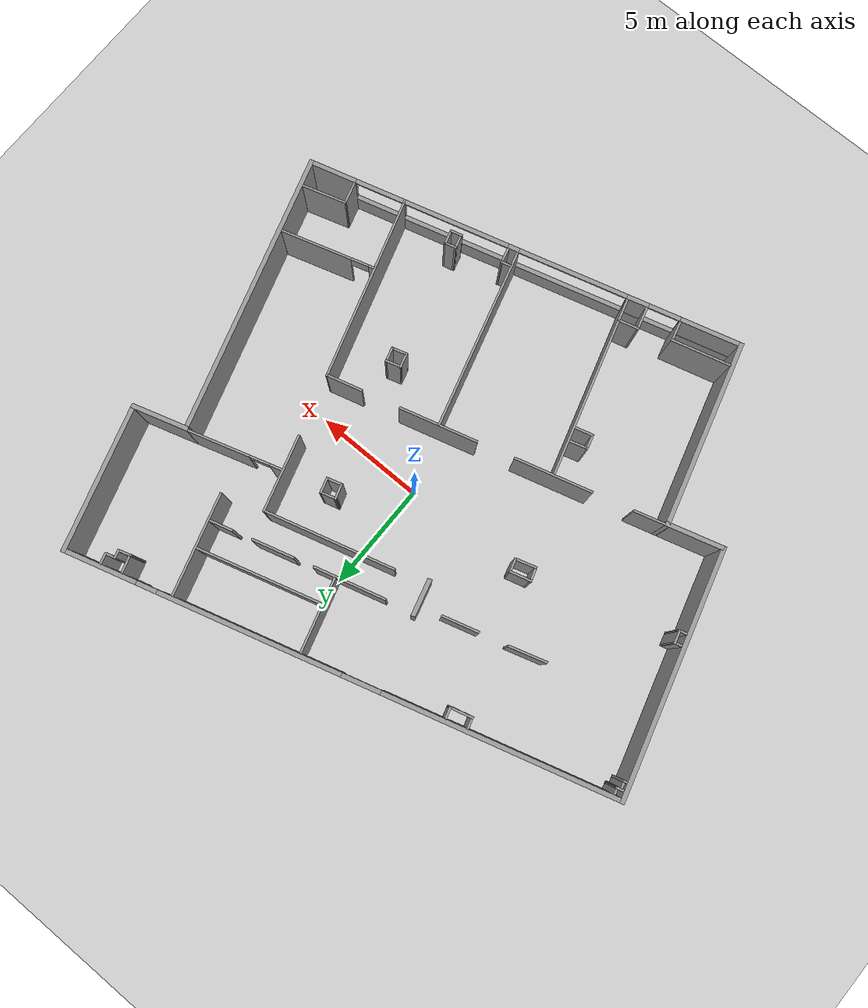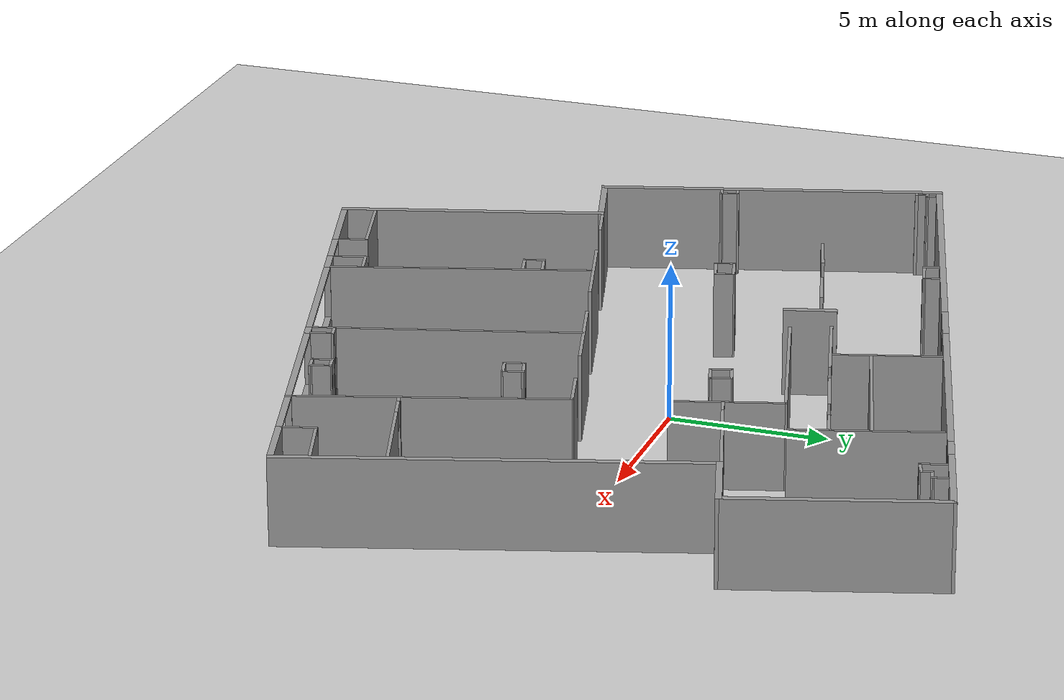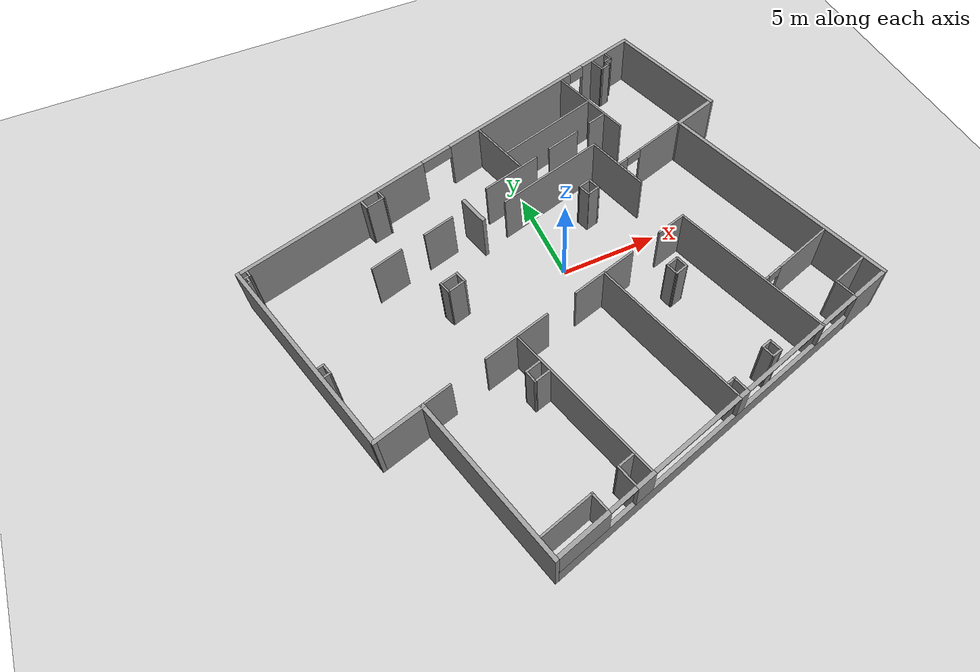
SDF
<?xml version='1.0'?>
<sdf version='1.4'>
  <world name='default'>
    <light name='sun' type='directional'>
      <cast_shadows>1</cast_shadows>
      <pose>0 0 10 0 -0 0</pose>
      <diffuse>0.8 0.8 0.8 1</diffuse>
      <specular>0.2 0.2 0.2 1</specular>
      <attenuation>
        <range>1000</range>
        <constant>0.9</constant>
        <linear>0.01</linear>
        <quadratic>0.001</quadratic>
      </attenuation>
      <direction>-0.5 0.1 -0.9</direction>
    </light>

    <model name='ground_plane'>
      <static>1</static>
      <link name='link'>
        <collision name='collision'>
          <geometry>
            <plane>
              <normal>0 0 1</normal>
              <size>100 100</size>
            </plane>
          </geometry>
          <surface>
            <friction>
              <ode>
                <mu>100</mu>
                <mu2>50</mu2>
              </ode>
            </friction>
            <bounce/>
            <contact>
              <ode/>
            </contact>
          </surface>
          <max_contacts>10</max_contacts>
        </collision>
        <visual name='visual'>
          <cast_shadows>0</cast_shadows>
          <geometry>
            <plane>
              <normal>0 0 1</normal>
              <size>100 100</size>
            </plane>
          </geometry>
          <material>
            <script>
              <uri>file://media/materials/scripts/gazebo.material</uri>
              <name>Gazebo/Grey</name>
            </script>
          </material>
        </visual>
        <velocity_decay>
          <linear>0</linear>
          <angular>0</angular>
        </velocity_decay>
        <self_collide>0</self_collide>
        <kinematic>0</kinematic>
        <gravity>1</gravity>
      </link>
    </model>

    <physics type="ode">
      <gravity>0.000000 0.000000 -9.810000</gravity>
      <ode>
        <solver>
          <type>quick</type>
          <iters>20</iters>
          <sor>1.000000</sor>
        </solver>
        <constraints>
          <cfm>0.000000</cfm>
          <erp>0.200000</erp>
          <contact_max_correcting_vel>100.000000</contact_max_correcting_vel>
          <contact_surface_layer>0.000000</contact_surface_layer>
        </constraints>
      </ode>
      <real_time_update_rate>1000.000000</real_time_update_rate>
      <max_step_size>0.001000</max_step_size>
      <real_time_factor>1.000000</real_time_factor>
      <max_contacts>20</max_contacts>
    </physics>

    <scene>
      <ambient>0.4 0.4 0.4 1</ambient>
      <background>0.7 0.7 0.7 1</background>
      <shadows>0</shadows>
    </scene>
    <spherical_coordinates>
      <surface_model>EARTH_WGS84</surface_model>
      <latitude_deg>0</latitude_deg>
      <longitude_deg>0</longitude_deg>
      <elevation>0</elevation>
      <heading_deg>0</heading_deg>
    </spherical_coordinates>
    <model name='PAL_office'>
      <pose>-1 -1 0 0 -0 0</pose>
      <link name='Wall_10'>
        <collision name='Wall_10_Collision'>
          <geometry>
            <box>
              <size>6.73478 0.2 2.78</size>
            </box>
          </geometry>
          <pose>0 0 1.39 0 -0 0</pose>
          <max_contacts>10</max_contacts>
          <surface>
            <bounce/>
            <friction>
              <ode/>
            </friction>
            <contact>
              <ode/>
            </contact>
          </surface>
        </collision>
        <visual name='Wall_10_Visual'>
          <pose>0 0 1.39 0 -0 0</pose>
          <geometry>
            <box>
              <size>6.73478 0.2 2.78</size>
            </box>
          </geometry>
          <material>
            <script>
              <uri>file://media/materials/scripts/gazebo.material</uri>
              <name>Gazebo/Grey</name>
            </script>
            <ambient>0.5 0.5 0.5 1</ambient>
          </material>
        </visual>
        <pose>11.1005 9.10601 0 0 -0 1.85624</pose>
        <velocity_decay>
          <linear>0</linear>
          <angular>0</angular>
        </velocity_decay>
        <self_collide>0</self_collide>
        <kinematic>0</kinematic>
        <gravity>1</gravity>
      </link>
      <link name='Wall_101'>
        <collision name='Wall_101_Collision'>
          <geometry>
            <box>
              <size>0.35 0.1 2.78</size>
            </box>
          </geometry>
          <pose>0 0 1.39 0 -0 0</pose>
          <max_contacts>10</max_contacts>
          <surface>
            <bounce/>
            <friction>
              <ode/>
            </friction>
            <contact>
              <ode/>
            </contact>
          </surface>
        </collision>
        <visual name='Wall_101_Visual'>
          <pose>0 0 1.39 0 -0 0</pose>
          <geometry>
            <box>
              <size>0.35 0.1 2.78</size>
            </box>
          </geometry>
          <material>
            <script>
              <uri>file://media/materials/scripts/gazebo.material</uri>
              <name>Gazebo/Grey</name>
            </script>
            <ambient>0.5 0.5 0.5 1</ambient>
          </material>
        </visual>
        <pose>-13.001 5.22701 0 0 0 -2.87429</pose>
        <velocity_decay>
          <linear>0</linear>
          <angular>0</angular>
        </velocity_decay>
        <self_collide>0</self_collide>
        <kinematic>0</kinematic>
        <gravity>1</gravity>
      </link>
      <link name='Wall_103'>
        <collision name='Wall_103_Collision'>
          <geometry>
            <box>
              <size>0.35 0.1 2.78</size>
            </box>
          </geometry>
          <pose>0 0 1.39 0 -0 0</pose>
          <max_contacts>10</max_contacts>
          <surface>
            <bounce/>
            <friction>
              <ode/>
            </friction>
            <contact>
              <ode/>
            </contact>
          </surface>
        </collision>
        <visual name='Wall_103_Visual'>
          <pose>0 0 1.39 0 -0 0</pose>
          <geometry>
            <box>
              <size>0.35 0.1 2.78</size>
            </box>
          </geometry>
          <material>
            <script>
              <uri>file://media/materials/scripts/gazebo.material</uri>
              <name>Gazebo/Grey</name>
            </script>
            <ambient>0.5 0.5 0.5 1</ambient>
          </material>
        </visual>
        <pose>-12.915 5.38001 0 0 -0 1.85075</pose>
        <velocity_decay>
          <linear>0</linear>
          <angular>0</angular>
        </velocity_decay>
        <self_collide>0</self_collide>
        <kinematic>0</kinematic>
        <gravity>1</gravity>
      </link>
      <link name='Wall_113'>
        <collision name='Wall_113_Collision'>
          <geometry>
            <box>
              <size>0.183 0.1 2.78</size>
            </box>
          </geometry>
          <pose>0 0 1.39 0 -0 0</pose>
          <max_contacts>10</max_contacts>
          <surface>
            <bounce/>
            <friction>
              <ode/>
            </friction>
            <contact>
              <ode/>
            </contact>
          </surface>
        </collision>
        <visual name='Wall_113_Visual'>
          <pose>0 0 1.39 0 -0 0</pose>
          <geometry>
            <box>
              <size>0.183 0.1 2.78</size>
            </box>
          </geometry>
          <material>
            <script>
              <uri>file://media/materials/scripts/gazebo.material</uri>
              <name>Gazebo/Grey</name>
            </script>
            <ambient>0.5 0.5 0.5 1</ambient>
          </material>
        </visual>
        <pose>-12.9885 4.88001 0 0 -0 0.268366</pose>
        <velocity_decay>
          <linear>0</linear>
          <angular>0</angular>
        </velocity_decay>
        <self_collide>0</self_collide>
        <kinematic>0</kinematic>
        <gravity>1</gravity>
      </link>
      <link name='Wall_118'>
        <collision name='Wall_118_Collision'>
          <geometry>
            <box>
              <size>0.252054 0.1 2.78</size>
            </box>
          </geometry>
          <pose>0 0 1.39 0 -0 0</pose>
          <max_contacts>10</max_contacts>
          <surface>
            <bounce/>
            <friction>
              <ode/>
            </friction>
            <contact>
              <ode/>
            </contact>
          </surface>
        </collision>
        <visual name='Wall_118_Visual'>
          <pose>0 0 1.39 0 -0 0</pose>
          <geometry>
            <box>
              <size>0.252054 0.1 2.78</size>
            </box>
          </geometry>
          <material>
            <script>
              <uri>file://media/materials/scripts/gazebo.material</uri>
              <name>Gazebo/Grey</name>
            </script>
            <ambient>0.5 0.5 0.5 1</ambient>
          </material>
        </visual>
        <pose>-12.996 5.05551 0 0 0 -1.31147</pose>
        <velocity_decay>
          <linear>0</linear>
          <angular>0</angular>
        </velocity_decay>
        <self_collide>0</self_collide>
        <kinematic>0</kinematic>
        <gravity>1</gravity>
      </link>
      <link name='Wall_12'>
        <collision name='Wall_12_Collision'>
          <geometry>
            <box>
              <size>2.648 0.2 2.78</size>
            </box>
          </geometry>
          <pose>0 0 1.39 0 -0 0</pose>
          <max_contacts>10</max_contacts>
          <surface>
            <bounce/>
            <friction>
              <ode/>
            </friction>
            <contact>
              <ode/>
            </contact>
          </surface>
        </collision>
        <visual name='Wall_12_Visual'>
          <pose>0 0 1.39 0 -0 0</pose>
          <geometry>
            <box>
              <size>2.648 0.2 2.78</size>
            </box>
          </geometry>
          <material>
            <script>
              <uri>file://media/materials/scripts/gazebo.material</uri>
              <name>Gazebo/Grey</name>
            </script>
            <ambient>0.5 0.5 0.5 1</ambient>
          </material>
        </visual>
        <pose>-9.23199 -4.61199 0 0 0 -2.8652</pose>
        <velocity_decay>
          <linear>0</linear>
          <angular>0</angular>
        </velocity_decay>
        <self_collide>0</self_collide>
        <kinematic>0</kinematic>
        <gravity>1</gravity>
      </link>
      <link name='Wall_121'>
        <collision name='Wall_121_Collision'>
          <geometry>
            <box>
              <size>1.01214 0.1 2.78</size>
            </box>
          </geometry>
          <pose>0 0 1.39 0 -0 0</pose>
          <max_contacts>10</max_contacts>
          <surface>
            <bounce/>
            <friction>
              <ode/>
            </friction>
            <contact>
              <ode/>
            </contact>
          </surface>
        </collision>
        <visual name='Wall_121_Visual'>
          <pose>0 0 1.39 0 -0 0</pose>
          <geometry>
            <box>
              <size>1.01214 0.1 2.78</size>
            </box>
          </geometry>
          <material>
            <script>
              <uri>file://media/materials/scripts/gazebo.material</uri>
              <name>Gazebo/Grey</name>
            </script>
            <ambient>0.5 0.5 0.5 1</ambient>
          </material>
        </visual>
        <pose>-4.76149 1.21201 0 0 -0 0.266252</pose>
        <velocity_decay>
          <linear>0</linear>
          <angular>0</angular>
        </velocity_decay>
        <self_collide>0</self_collide>
        <kinematic>0</kinematic>
        <gravity>1</gravity>
      </link>
      <link name='Wall_122'>
        <collision name='Wall_122_Collision'>
          <geometry>
            <box>
              <size>0.660446 0.1 2.78</size>
            </box>
          </geometry>
          <pose>0 0 1.39 0 -0 0</pose>
          <max_contacts>10</max_contacts>
          <surface>
            <bounce/>
            <friction>
              <ode/>
            </friction>
            <contact>
              <ode/>
            </contact>
          </surface>
        </collision>
        <visual name='Wall_122_Visual'>
          <pose>0 0 1.39 0 -0 0</pose>
          <geometry>
            <box>
              <size>0.660446 0.1 2.78</size>
            </box>
          </geometry>
          <material>
            <script>
              <uri>file://media/materials/scripts/gazebo.material</uri>
              <name>Gazebo/Grey</name>
            </script>
            <ambient>0.5 0.5 0.5 1</ambient>
          </material>
        </visual>
        <pose>-4.24649 1.06201 0 0 0 -1.29985</pose>
        <velocity_decay>
          <linear>0</linear>
          <angular>0</angular>
        </velocity_decay>
        <self_collide>0</self_collide>
        <kinematic>0</kinematic>
        <gravity>1</gravity>
      </link>
      <link name='Wall_127'>
        <collision name='Wall_127_Collision'>
          <geometry>
            <box>
              <size>0.678705 0.1 2.78</size>
            </box>
          </geometry>
          <pose>0 0 1.39 0 -0 0</pose>
          <max_contacts>10</max_contacts>
          <surface>
            <bounce/>
            <friction>
              <ode/>
            </friction>
            <contact>
              <ode/>
            </contact>
          </surface>
        </collision>
        <visual name='Wall_127_Visual'>
          <pose>0 0 1.39 0 -0 0</pose>
          <geometry>
            <box>
              <size>0.678705 0.1 2.78</size>
            </box>
          </geometry>
          <material>
            <script>
              <uri>file://media/materials/scripts/gazebo.material</uri>
              <name>Gazebo/Grey</name>
            </script>
            <ambient>0.5 0.5 0.5 1</ambient>
          </material>
        </visual>
        <pose>-5.11149 0.817011 0 0 0 -1.25451</pose>
        <velocity_decay>
          <linear>0</linear>
          <angular>0</angular>
        </velocity_decay>
        <self_collide>0</self_collide>
        <kinematic>0</kinematic>
        <gravity>1</gravity>
      </link>
      <link name='Wall_128'>
        <collision name='Wall_128_Collision'>
          <geometry>
            <box>
              <size>0.913204 0.1 2.78</size>
            </box>
          </geometry>
          <pose>0 0 1.39 0 -0 0</pose>
          <max_contacts>10</max_contacts>
          <surface>
            <bounce/>
            <friction>
              <ode/>
            </friction>
            <contact>
              <ode/>
            </contact>
          </surface>
        </collision>
        <visual name='Wall_128_Visual'>
          <pose>0 0 1.39 0 -0 0</pose>
          <geometry>
            <box>
              <size>0.913204 0.1 2.78</size>
            </box>
          </geometry>
          <material>
            <script>
              <uri>file://media/materials/scripts/gazebo.material</uri>
              <name>Gazebo/Grey</name>
            </script>
            <ambient>0.5 0.5 0.5 1</ambient>
          </material>
        </visual>
        <pose>-4.63149 0.657011 0 0 -0 0.286745</pose>
        <velocity_decay>
          <linear>0</linear>
          <angular>0</angular>
        </velocity_decay>
        <self_collide>0</self_collide>
        <kinematic>0</kinematic>
        <gravity>1</gravity>
      </link>
      <link name='Wall_133'>
        <collision name='Wall_133_Collision'>
          <geometry>
            <box>
              <size>0.754498 0.1 2.78</size>
            </box>
          </geometry>
          <pose>0 0 1.39 0 -0 0</pose>
          <max_contacts>10</max_contacts>
          <surface>
            <bounce/>
            <friction>
              <ode/>
            </friction>
            <contact>
              <ode/>
            </contact>
          </surface>
        </collision>
        <visual name='Wall_133_Visual'>
          <pose>0 0 1.39 0 -0 0</pose>
          <geometry>
            <box>
              <size>0.754498 0.1 2.78</size>
            </box>
          </geometry>
          <material>
            <script>
              <uri>file://media/materials/scripts/gazebo.material</uri>
              <name>Gazebo/Grey</name>
            </script>
            <ambient>0.5 0.5 0.5 1</ambient>
          </material>
        </visual>
        <pose>3.37451 3.66401 0 0 -0 0.275362</pose>
        <velocity_decay>
          <linear>0</linear>
          <angular>0</angular>
        </velocity_decay>
        <self_collide>0</self_collide>
        <kinematic>0</kinematic>
        <gravity>1</gravity>
      </link>
      <link name='Wall_134'>
        <collision name='Wall_134_Collision'>
          <geometry>
            <box>
              <size>0.726947 0.1 2.78</size>
            </box>
          </geometry>
          <pose>0 0 1.39 0 -0 0</pose>
          <max_contacts>10</max_contacts>
          <surface>
            <bounce/>
            <friction>
              <ode/>
            </friction>
            <contact>
              <ode/>
            </contact>
          </surface>
        </collision>
        <visual name='Wall_134_Visual'>
          <pose>0 0 1.39 0 -0 0</pose>
          <geometry>
            <box>
              <size>0.726947 0.1 2.78</size>
            </box>
          </geometry>
          <material>
            <script>
              <uri>file://media/materials/scripts/gazebo.material</uri>
              <name>Gazebo/Grey</name>
            </script>
            <ambient>0.5 0.5 0.5 1</ambient>
          </material>
        </visual>
        <pose>3.77951 3.45301 0 0 0 -1.27934</pose>
        <velocity_decay>
          <linear>0</linear>
          <angular>0</angular>
        </velocity_decay>
        <self_collide>0</self_collide>
        <kinematic>0</kinematic>
        <gravity>1</gravity>
      </link>
      <link name='Wall_14'>
        <collision name='Wall_14_Collision'>
          <geometry>
            <box>
              <size>8.475 0.2 2.78</size>
            </box>
          </geometry>
          <pose>0 0 1.39 0 -0 0</pose>
          <max_contacts>10</max_contacts>
          <surface>
            <bounce/>
            <friction>
              <ode/>
            </friction>
            <contact>
              <ode/>
            </contact>
          </surface>
        </collision>
        <visual name='Wall_14_Visual'>
          <pose>0 0 1.39 0 -0 0</pose>
          <geometry>
            <box>
              <size>8.475 0.2 2.78</size>
            </box>
          </geometry>
          <material>
            <script>
              <uri>file://media/materials/scripts/gazebo.material</uri>
              <name>Gazebo/Grey</name>
            </script>
            <ambient>0.5 0.5 0.5 1</ambient>
          </material>
        </visual>
        <pose>-6.93049 -8.25999 0 0 0 -1.29568</pose>
        <velocity_decay>
          <linear>0</linear>
          <angular>0</angular>
        </velocity_decay>
        <self_collide>0</self_collide>
        <kinematic>0</kinematic>
        <gravity>1</gravity>
      </link>
      <link name='Wall_140'>
        <collision name='Wall_140_Collision'>
          <geometry>
            <box>
              <size>0.729033 0.1 2.78</size>
            </box>
          </geometry>
          <pose>0 0 1.39 0 -0 0</pose>
          <max_contacts>10</max_contacts>
          <surface>
            <bounce/>
            <friction>
              <ode/>
            </friction>
            <contact>
              <ode/>
            </contact>
          </surface>
        </collision>
        <visual name='Wall_140_Visual'>
          <pose>0 0 1.39 0 -0 0</pose>
          <geometry>
            <box>
              <size>0.729033 0.1 2.78</size>
            </box>
          </geometry>
          <material>
            <script>
              <uri>file://media/materials/scripts/gazebo.material</uri>
              <name>Gazebo/Grey</name>
            </script>
            <ambient>0.5 0.5 0.5 1</ambient>
          </material>
        </visual>
        <pose>3.15251 3.27451 0 0 0 -1.27066</pose>
        <velocity_decay>
          <linear>0</linear>
          <angular>0</angular>
        </velocity_decay>
        <self_collide>0</self_collide>
        <kinematic>0</kinematic>
        <gravity>1</gravity>
      </link>
      <link name='Wall_142'>
        <collision name='Wall_142_Collision'>
          <geometry>
            <box>
              <size>0.721105 0.1 2.78</size>
            </box>
          </geometry>
          <pose>0 0 1.39 0 -0 0</pose>
          <max_contacts>10</max_contacts>
          <surface>
            <bounce/>
            <friction>
              <ode/>
            </friction>
            <contact>
              <ode/>
            </contact>
          </surface>
        </collision>
        <visual name='Wall_142_Visual'>
          <pose>0 0 1.39 0 -0 0</pose>
          <geometry>
            <box>
              <size>0.721105 0.1 2.78</size>
            </box>
          </geometry>
          <material>
            <script>
              <uri>file://media/materials/scripts/gazebo.material</uri>
              <name>Gazebo/Grey</name>
            </script>
            <ambient>0.5 0.5 0.5 1</ambient>
          </material>
        </visual>
        <pose>3.57151 3.06601 0 0 0 -2.85754</pose>
        <velocity_decay>
          <linear>0</linear>
          <angular>0</angular>
        </velocity_decay>
        <self_collide>0</self_collide>
        <kinematic>0</kinematic>
        <gravity>1</gravity>
      </link>
      <link name='Wall_145'>
        <collision name='Wall_145_Collision'>
          <geometry>
            <box>
              <size>8.27375 0.1 2.78</size>
            </box>
          </geometry>
          <pose>0 0 1.39 0 -0 0</pose>
          <max_contacts>10</max_contacts>
          <surface>
            <bounce/>
            <friction>
              <ode/>
            </friction>
            <contact>
              <ode/>
            </contact>
          </surface>
        </collision>
        <visual name='Wall_145_Visual'>
          <pose>0 0 1.39 0 -0 0</pose>
          <geometry>
            <box>
              <size>8.27375 0.1 2.78</size>
            </box>
          </geometry>
          <material>
            <script>
              <uri>file://media/materials/scripts/gazebo.material</uri>
              <name>Gazebo/Grey</name>
            </script>
            <ambient>0.5 0.5 0.5 1</ambient>
          </material>
        </visual>
        <pose>7.88901 -4.08549 0 0 0 -1.27598</pose>
        <velocity_decay>
          <linear>0</linear>
          <angular>0</angular>
        </velocity_decay>
        <self_collide>0</self_collide>
        <kinematic>0</kinematic>
        <gravity>1</gravity>
      </link>
      <link name='Wall_147'>
        <collision name='Wall_147_Collision'>
          <geometry>
            <box>
              <size>1.6624 0.1 2.78</size>
            </box>
          </geometry>
          <pose>0 0 1.39 0 -0 0</pose>
          <max_contacts>10</max_contacts>
          <surface>
            <bounce/>
            <friction>
              <ode/>
            </friction>
            <contact>
              <ode/>
            </contact>
          </surface>
        </collision>
        <visual name='Wall_147_Visual'>
          <pose>0 0 1.39 0 -0 0</pose>
          <geometry>
            <box>
              <size>1.6624 0.1 2.78</size>
            </box>
          </geometry>
          <material>
            <script>
              <uri>file://media/materials/scripts/gazebo.material</uri>
              <name>Gazebo/Grey</name>
            </script>
            <ambient>0.5 0.5 0.5 1</ambient>
          </material>
        </visual>
        <pose>5.94751 -0.379989 0 0 0 -2.87613</pose>
        <velocity_decay>
          <linear>0</linear>
          <angular>0</angular>
        </velocity_decay>
        <self_collide>0</self_collide>
        <kinematic>0</kinematic>
        <gravity>1</gravity>
      </link>
      <link name='Wall_150'>
        <pose>10.26 -4.39249 0 0 -0 0.289894</pose>
        <visual name='Wall_150_Visual_0'>
          <pose>-2.03127 0 1.39 0 -0 0</pose>
          <geometry>
            <box>
              <size>0.2671 0.1 2.78</size>
            </box>
          </geometry>
          <material>
            <script>
              <uri>file://media/materials/scripts/gazebo.material</uri>
              <name>Gazebo/Grey</name>
            </script>
            <ambient>0.5 0.5 0.5 1</ambient>
          </material>
        </visual>
        <collision name='Wall_150_Collision_0'>
          <geometry>
            <box>
              <size>0.2671 0.1 2.78</size>
            </box>
          </geometry>
          <pose>-2.03127 0 1.39 0 -0 0</pose>
          <max_contacts>10</max_contacts>
          <surface>
            <bounce/>
            <friction>
              <ode/>
            </friction>
            <contact>
              <ode/>
            </contact>
          </surface>
        </collision>
        <visual name='Wall_150_Visual_1'>
          <pose>0.54355 0 1.39 0 -0 0</pose>
          <geometry>
            <box>
              <size>3.24255 0.1 2.78</size>
            </box>
          </geometry>
          <material>
            <script>
              <uri>file://media/materials/scripts/gazebo.material</uri>
              <name>Gazebo/Grey</name>
            </script>
            <ambient>0.5 0.5 0.5 1</ambient>
          </material>
        </visual>
        <collision name='Wall_150_Collision_1'>
          <geometry>
            <box>
              <size>3.24255 0.1 2.78</size>
            </box>
          </geometry>
          <pose>0.54355 0 1.39 0 -0 0</pose>
          <max_contacts>10</max_contacts>
          <surface>
            <bounce/>
            <friction>
              <ode/>
            </friction>
            <contact>
              <ode/>
            </contact>
          </surface>
        </collision>
        <visual name='Wall_150_Visual_2'>
          <pose>-1.48772 0 2.44 0 -0 0</pose>
          <geometry>
            <box>
              <size>0.82 0.1 0.68</size>
            </box>
          </geometry>
          <material>
            <script>
              <uri>file://media/materials/scripts/gazebo.material</uri>
              <name>Gazebo/Grey</name>
            </script>
            <ambient>0.5 0.5 0.5 1</ambient>
          </material>
        </visual>
        <collision name='Wall_150_Collision_2'>
          <geometry>
            <box>
              <size>0.82 0.1 0.68</size>
            </box>
          </geometry>
          <pose>-1.48772 0 2.44 0 -0 0</pose>
          <max_contacts>10</max_contacts>
          <surface>
            <bounce/>
            <friction>
              <ode/>
            </friction>
            <contact>
              <ode/>
            </contact>
          </surface>
        </collision>
        <velocity_decay>
          <linear>0</linear>
          <angular>0</angular>
        </velocity_decay>
        <self_collide>0</self_collide>
        <kinematic>0</kinematic>
        <gravity>1</gravity>
      </link>
      <link name='Wall_153'>
        <collision name='Wall_153_Collision'>
          <geometry>
            <box>
              <size>2.08407 0.1 2.78</size>
            </box>
          </geometry>
          <pose>0 0 1.39 0 -0 0</pose>
          <max_contacts>10</max_contacts>
          <surface>
            <bounce/>
            <friction>
              <ode/>
            </friction>
            <contact>
              <ode/>
            </contact>
          </surface>
        </collision>
        <visual name='Wall_153_Visual'>
          <pose>0 0 1.39 0 -0 0</pose>
          <geometry>
            <box>
              <size>2.08407 0.1 2.78</size>
            </box>
          </geometry>
          <material>
            <script>
              <uri>file://media/materials/scripts/gazebo.material</uri>
              <name>Gazebo/Grey</name>
            </script>
            <ambient>0.5 0.5 0.5 1</ambient>
          </material>
        </visual>
        <pose>11.9955 -6.18599 0 0 0 -2.85014</pose>
        <velocity_decay>
          <linear>0</linear>
          <angular>0</angular>
        </velocity_decay>
        <self_collide>0</self_collide>
        <kinematic>0</kinematic>
        <gravity>1</gravity>
      </link>
      <link name='Wall_154'>
        <collision name='Wall_154_Collision'>
          <geometry>
            <box>
              <size>1.04397 0.1 2.78</size>
            </box>
          </geometry>
          <pose>0 0 1.39 0 -0 0</pose>
          <max_contacts>10</max_contacts>
          <surface>
            <bounce/>
            <friction>
              <ode/>
            </friction>
            <contact>
              <ode/>
            </contact>
          </surface>
        </collision>
        <visual name='Wall_154_Visual'>
          <pose>0 0 1.39 0 -0 0</pose>
          <geometry>
            <box>
              <size>1.04397 0.1 2.78</size>
            </box>
          </geometry>
          <material>
            <script>
              <uri>file://media/materials/scripts/gazebo.material</uri>
              <name>Gazebo/Grey</name>
            </script>
            <ambient>0.5 0.5 0.5 1</ambient>
          </material>
        </visual>
        <pose>11.176 -6.92449 0 0 0 -1.29061</pose>
        <velocity_decay>
          <linear>0</linear>
          <angular>0</angular>
        </velocity_decay>
        <self_collide>0</self_collide>
        <kinematic>0</kinematic>
        <gravity>1</gravity>
      </link>
      <link name='Wall_158'>
        <collision name='Wall_158_Collision'>
          <geometry>
            <box>
              <size>3.52366 0.1 2.78</size>
            </box>
          </geometry>
          <pose>0 0 1.39 0 -0 0</pose>
          <max_contacts>10</max_contacts>
          <surface>
            <bounce/>
            <friction>
              <ode/>
            </friction>
            <contact>
              <ode/>
            </contact>
          </surface>
        </collision>
        <visual name='Wall_158_Visual'>
          <pose>0 0 1.39 0 -0 0</pose>
          <geometry>
            <box>
              <size>3.52366 0.1 2.78</size>
            </box>
          </geometry>
          <material>
            <script>
              <uri>file://media/materials/scripts/gazebo.material</uri>
              <name>Gazebo/Grey</name>
            </script>
            <ambient>0.5 0.5 0.5 1</ambient>
          </material>
        </visual>
        <pose>-3.20649 -2.89249 0 0 -0 0.269352</pose>
        <velocity_decay>
          <linear>0</linear>
          <angular>0</angular>
        </velocity_decay>
        <self_collide>0</self_collide>
        <kinematic>0</kinematic>
        <gravity>1</gravity>
      </link>
      <link name='Wall_16'>
        <pose>3.78351 -9.59399 0 0 0 -2.87199</pose>
        <visual name='Wall_16_Visual_0'>
          <pose>-8.83974 0 1.39 0 -0 0</pose>
          <geometry>
            <box>
              <size>2.04382 0.2 2.78</size>
            </box>
          </geometry>
          <material>
            <script>
              <uri>file://media/materials/scripts/gazebo.material</uri>
              <name>Gazebo/Grey</name>
            </script>
            <ambient>0.5 0.5 0.5 1</ambient>
          </material>
        </visual>
        <collision name='Wall_16_Collision_0'>
          <geometry>
            <box>
              <size>2.04382 0.2 2.78</size>
            </box>
          </geometry>
          <pose>-8.83974 0 1.39 0 -0 0</pose>
          <max_contacts>10</max_contacts>
          <surface>
            <bounce/>
            <friction>
              <ode/>
            </friction>
            <contact>
              <ode/>
            </contact>
          </surface>
        </collision>
        <visual name='Wall_16_Visual_1'>
          <pose>1.02191 0 0.55 0 -0 0</pose>
          <geometry>
            <box>
              <size>17.6795 0.2 1.1</size>
            </box>
          </geometry>
          <material>
            <script>
              <uri>file://media/materials/scripts/gazebo.material</uri>
              <name>Gazebo/Grey</name>
            </script>
            <ambient>0.5 0.5 0.5 1</ambient>
          </material>
        </visual>
        <collision name='Wall_16_Collision_1'>
          <geometry>
            <box>
              <size>17.6795 0.2 1.1</size>
            </box>
          </geometry>
          <pose>1.02191 0 0.55 0 -0 0</pose>
          <max_contacts>10</max_contacts>
          <surface>
            <bounce/>
            <friction>
              <ode/>
            </friction>
            <contact>
              <ode/>
            </contact>
          </surface>
        </collision>
        <visual name='Wall_16_Visual_2'>
          <pose>-5.54535 0 1.94 0 -0 0</pose>
          <geometry>
            <box>
              <size>0.100368 0.2 1.68</size>
            </box>
          </geometry>
          <material>
            <script>
              <uri>file://media/materials/scripts/gazebo.material</uri>
              <name>Gazebo/Grey</name>
            </script>
            <ambient>0.5 0.5 0.5 1</ambient>
          </material>
        </visual>
        <collision name='Wall_16_Collision_2'>
          <geometry>
            <box>
              <size>0.100368 0.2 1.68</size>
            </box>
          </geometry>
          <pose>-5.54535 0 1.94 0 -0 0</pose>
          <max_contacts>10</max_contacts>
          <surface>
            <bounce/>
            <friction>
              <ode/>
            </friction>
            <contact>
              <ode/>
            </contact>
          </surface>
        </collision>
        <visual name='Wall_16_Visual_3'>
          <pose>-0.435842 0 1.94 0 -0 0</pose>
          <geometry>
            <box>
              <size>0.509797 0.2 1.68</size>
            </box>
          </geometry>
          <material>
            <script>
              <uri>file://media/materials/scripts/gazebo.material</uri>
              <name>Gazebo/Grey</name>
            </script>
            <ambient>0.5 0.5 0.5 1</ambient>
          </material>
        </visual>
        <collision name='Wall_16_Collision_3'>
          <geometry>
            <box>
              <size>0.509797 0.2 1.68</size>
            </box>
          </geometry>
          <pose>-0.435842 0 1.94 0 -0 0</pose>
          <max_contacts>10</max_contacts>
          <surface>
            <bounce/>
            <friction>
              <ode/>
            </friction>
            <contact>
              <ode/>
            </contact>
          </surface>
        </collision>
        <visual name='Wall_16_Visual_4'>
          <pose>5.27686 0 1.94 0 -0 0</pose>
          <geometry>
            <box>
              <size>0.994619 0.2 1.68</size>
            </box>
          </geometry>
          <material>
            <script>
              <uri>file://media/materials/scripts/gazebo.material</uri>
              <name>Gazebo/Grey</name>
            </script>
            <ambient>0.5 0.5 0.5 1</ambient>
          </material>
        </visual>
        <collision name='Wall_16_Collision_4'>
          <geometry>
            <box>
              <size>0.994619 0.2 1.68</size>
            </box>
          </geometry>
          <pose>5.27686 0 1.94 0 -0 0</pose>
          <max_contacts>10</max_contacts>
          <surface>
            <bounce/>
            <friction>
              <ode/>
            </friction>
            <contact>
              <ode/>
            </contact>
          </surface>
        </collision>
        <visual name='Wall_16_Visual_5'>
          <pose>8.53741 0 1.94 0 -0 0</pose>
          <geometry>
            <box>
              <size>2.64848 0.2 1.68</size>
            </box>
          </geometry>
          <material>
            <script>
              <uri>file://media/materials/scripts/gazebo.material</uri>
              <name>Gazebo/Grey</name>
            </script>
            <ambient>0.5 0.5 0.5 1</ambient>
          </material>
        </visual>
        <collision name='Wall_16_Collision_5'>
          <geometry>
            <box>
              <size>2.64848 0.2 1.68</size>
            </box>
          </geometry>
          <pose>8.53741 0 1.94 0 -0 0</pose>
          <max_contacts>10</max_contacts>
          <surface>
            <bounce/>
            <friction>
              <ode/>
            </friction>
            <contact>
              <ode/>
            </contact>
          </surface>
        </collision>
        <visual name='Wall_16_Visual_6'>
          <pose>-6.70668 0 2.74 0 -0 0</pose>
          <geometry>
            <box>
              <size>2.22229 0.2 0.08</size>
            </box>
          </geometry>
          <material>
            <script>
              <uri>file://media/materials/scripts/gazebo.material</uri>
              <name>Gazebo/Grey</name>
            </script>
            <ambient>0.5 0.5 0.5 1</ambient>
          </material>
        </visual>
        <collision name='Wall_16_Collision_6'>
          <geometry>
            <box>
              <size>2.22229 0.2 0.08</size>
            </box>
          </geometry>
          <pose>-6.70668 0 2.74 0 -0 0</pose>
          <max_contacts>10</max_contacts>
          <surface>
            <bounce/>
            <friction>
              <ode/>
            </friction>
            <contact>
              <ode/>
            </contact>
          </surface>
        </collision>
        <visual name='Wall_16_Visual_7'>
          <pose>-3.09295 0 2.74 0 -0 0</pose>
          <geometry>
            <box>
              <size>4.80443 0.2 0.08</size>
            </box>
          </geometry>
          <material>
            <script>
              <uri>file://media/materials/scripts/gazebo.material</uri>
              <name>Gazebo/Grey</name>
            </script>
            <ambient>0.5 0.5 0.5 1</ambient>
          </material>
        </visual>
        <collision name='Wall_16_Collision_7'>
          <geometry>
            <box>
              <size>4.80443 0.2 0.08</size>
            </box>
          </geometry>
          <pose>-3.09295 0 2.74 0 -0 0</pose>
          <max_contacts>10</max_contacts>
          <surface>
            <bounce/>
            <friction>
              <ode/>
            </friction>
            <contact>
              <ode/>
            </contact>
          </surface>
        </collision>
        <visual name='Wall_16_Visual_8'>
          <pose>2.2993 0 2.74 0 -0 0</pose>
          <geometry>
            <box>
              <size>4.96049 0.2 0.08</size>
            </box>
          </geometry>
          <material>
            <script>
              <uri>file://media/materials/scripts/gazebo.material</uri>
              <name>Gazebo/Grey</name>
            </script>
            <ambient>0.5 0.5 0.5 1</ambient>
          </material>
        </visual>
        <collision name='Wall_16_Collision_8'>
          <geometry>
            <box>
              <size>4.96049 0.2 0.08</size>
            </box>
          </geometry>
          <pose>2.2993 0 2.74 0 -0 0</pose>
          <max_contacts>10</max_contacts>
          <surface>
            <bounce/>
            <friction>
              <ode/>
            </friction>
            <contact>
              <ode/>
            </contact>
          </surface>
        </collision>
        <visual name='Wall_16_Visual_9'>
          <pose>6.49367 0 2.74 0 -0 0</pose>
          <geometry>
            <box>
              <size>1.439 0.2 0.08</size>
            </box>
          </geometry>
          <material>
            <script>
              <uri>file://media/materials/scripts/gazebo.material</uri>
              <name>Gazebo/Grey</name>
            </script>
            <ambient>0.5 0.5 0.5 1</ambient>
          </material>
        </visual>
        <collision name='Wall_16_Collision_9'>
          <geometry>
            <box>
              <size>1.439 0.2 0.08</size>
            </box>
          </geometry>
          <pose>6.49367 0 2.74 0 -0 0</pose>
          <max_contacts>10</max_contacts>
          <surface>
            <bounce/>
            <friction>
              <ode/>
            </friction>
            <contact>
              <ode/>
            </contact>
          </surface>
        </collision>
        <velocity_decay>
          <linear>0</linear>
          <angular>0</angular>
        </velocity_decay>
        <self_collide>0</self_collide>
        <kinematic>0</kinematic>
        <gravity>1</gravity>
      </link>
      <link name='Wall_160'>
        <collision name='Wall_160_Collision'>
          <geometry>
            <box>
              <size>3.56369 0.1 2.78</size>
            </box>
          </geometry>
          <pose>0 0 1.39 0 -0 0</pose>
          <max_contacts>10</max_contacts>
          <surface>
            <bounce/>
            <friction>
              <ode/>
            </friction>
            <contact>
              <ode/>
            </contact>
          </surface>
        </collision>
        <visual name='Wall_160_Visual'>
          <pose>0 0 1.39 0 -0 0</pose>
          <geometry>
            <box>
              <size>3.56369 0.1 2.78</size>
            </box>
          </geometry>
          <material>
            <script>
              <uri>file://media/materials/scripts/gazebo.material</uri>
              <name>Gazebo/Grey</name>
            </script>
            <ambient>0.5 0.5 0.5 1</ambient>
          </material>
        </visual>
        <pose>1.79301 -1.50349 0 0 -0 0.269139</pose>
        <velocity_decay>
          <linear>0</linear>
          <angular>0</angular>
        </velocity_decay>
        <self_collide>0</self_collide>
        <kinematic>0</kinematic>
        <gravity>1</gravity>
      </link>
      <link name='Wall_162'>
        <collision name='Wall_162_Collision'>
          <geometry>
            <box>
              <size>1.39174 0.1 2.78</size>
            </box>
          </geometry>
          <pose>0 0 1.39 0 -0 0</pose>
          <max_contacts>10</max_contacts>
          <surface>
            <bounce/>
            <friction>
              <ode/>
            </friction>
            <contact>
              <ode/>
            </contact>
          </surface>
        </collision>
        <visual name='Wall_162_Visual'>
          <pose>0 0 1.39 0 -0 0</pose>
          <geometry>
            <box>
              <size>1.39174 0.1 2.78</size>
            </box>
          </geometry>
          <material>
            <script>
              <uri>file://media/materials/scripts/gazebo.material</uri>
              <name>Gazebo/Grey</name>
            </script>
            <ambient>0.5 0.5 0.5 1</ambient>
          </material>
        </visual>
        <pose>-7.30849 -4.02049 0 0 0 -2.86808</pose>
        <velocity_decay>
          <linear>0</linear>
          <angular>0</angular>
        </velocity_decay>
        <self_collide>0</self_collide>
        <kinematic>0</kinematic>
        <gravity>1</gravity>
      </link>
      <link name='Wall_164'>
        <collision name='Wall_164_Collision'>
          <geometry>
            <box>
              <size>8.25895 0.1 2.78</size>
            </box>
          </geometry>
          <pose>0 0 1.39 0 -0 0</pose>
          <max_contacts>10</max_contacts>
          <surface>
            <bounce/>
            <friction>
              <ode/>
            </friction>
            <contact>
              <ode/>
            </contact>
          </surface>
        </collision>
        <visual name='Wall_164_Visual'>
          <pose>0 0 1.39 0 -0 0</pose>
          <geometry>
            <box>
              <size>8.25895 0.1 2.78</size>
            </box>
          </geometry>
          <material>
            <script>
              <uri>file://media/materials/scripts/gazebo.material</uri>
              <name>Gazebo/Grey</name>
            </script>
            <ambient>0.5 0.5 0.5 1</ambient>
          </material>
        </visual>
        <pose>2.85601 -5.47899 0 0 0 -1.3012</pose>
        <velocity_decay>
          <linear>0</linear>
          <angular>0</angular>
        </velocity_decay>
        <self_collide>0</self_collide>
        <kinematic>0</kinematic>
        <gravity>1</gravity>
      </link>
      <link name='Wall_166'>
        <collision name='Wall_166_Collision'>
          <geometry>
            <box>
              <size>8.22 0.1 2.78</size>
            </box>
          </geometry>
          <pose>0 0 1.39 0 -0 0</pose>
          <max_contacts>10</max_contacts>
          <surface>
            <bounce/>
            <friction>
              <ode/>
            </friction>
            <contact>
              <ode/>
            </contact>
          </surface>
        </collision>
        <visual name='Wall_166_Visual'>
          <pose>0 0 1.39 0 -0 0</pose>
          <geometry>
            <box>
              <size>8.22 0.1 2.78</size>
            </box>
          </geometry>
          <material>
            <script>
              <uri>file://media/materials/scripts/gazebo.material</uri>
              <name>Gazebo/Grey</name>
            </script>
            <ambient>0.5 0.5 0.5 1</ambient>
          </material>
        </visual>
        <pose>-2.06049 -6.85199 0 0 0 -1.28668</pose>
        <velocity_decay>
          <linear>0</linear>
          <angular>0</angular>
        </velocity_decay>
        <self_collide>0</self_collide>
        <kinematic>0</kinematic>
        <gravity>1</gravity>
      </link>
      <link name='Wall_168'>
        <collision name='Wall_168_Collision'>
          <geometry>
            <box>
              <size>0.743567 0.1 2.78</size>
            </box>
          </geometry>
          <pose>0 0 1.39 0 -0 0</pose>
          <max_contacts>10</max_contacts>
          <surface>
            <bounce/>
            <friction>
              <ode/>
            </friction>
            <contact>
              <ode/>
            </contact>
          </surface>
        </collision>
        <visual name='Wall_168_Visual'>
          <pose>0 0 1.39 0 -0 0</pose>
          <geometry>
            <box>
              <size>0.743567 0.1 2.78</size>
            </box>
          </geometry>
          <material>
            <script>
              <uri>file://media/materials/scripts/gazebo.material</uri>
              <name>Gazebo/Grey</name>
            </script>
            <ambient>0.5 0.5 0.5 1</ambient>
          </material>
        </visual>
        <pose>4.88801 -2.31549 0 0 -0 0.288331</pose>
        <velocity_decay>
          <linear>0</linear>
          <angular>0</angular>
        </velocity_decay>
        <self_collide>0</self_collide>
        <kinematic>0</kinematic>
        <gravity>1</gravity>
      </link>
      <link name='Wall_169'>
        <collision name='Wall_169_Collision'>
          <geometry>
            <box>
              <size>0.700613 0.1 2.78</size>
            </box>
          </geometry>
          <pose>0 0 1.39 0 -0 0</pose>
          <max_contacts>10</max_contacts>
          <surface>
            <bounce/>
            <friction>
              <ode/>
            </friction>
            <contact>
              <ode/>
            </contact>
          </surface>
        </collision>
        <visual name='Wall_169_Visual'>
          <pose>0 0 1.39 0 -0 0</pose>
          <geometry>
            <box>
              <size>0.700613 0.1 2.78</size>
            </box>
          </geometry>
          <material>
            <script>
              <uri>file://media/materials/scripts/gazebo.material</uri>
              <name>Gazebo/Grey</name>
            </script>
            <ambient>0.5 0.5 0.5 1</ambient>
          </material>
        </visual>
        <pose>5.27451 -2.51399 0 0 0 -1.30805</pose>
        <velocity_decay>
          <linear>0</linear>
          <angular>0</angular>
        </velocity_decay>
        <self_collide>0</self_collide>
        <kinematic>0</kinematic>
        <gravity>1</gravity>
      </link>
      <link name='Wall_171'>
        <collision name='Wall_171_Collision'>
          <geometry>
            <box>
              <size>0.699643 0.1 2.78</size>
            </box>
          </geometry>
          <pose>0 0 1.39 0 -0 0</pose>
          <max_contacts>10</max_contacts>
          <surface>
            <bounce/>
            <friction>
              <ode/>
            </friction>
            <contact>
              <ode/>
            </contact>
          </surface>
        </collision>
        <visual name='Wall_171_Visual'>
          <pose>0 0 1.39 0 -0 0</pose>
          <geometry>
            <box>
              <size>0.699643 0.1 2.78</size>
            </box>
          </geometry>
          <material>
            <script>
              <uri>file://media/materials/scripts/gazebo.material</uri>
              <name>Gazebo/Grey</name>
            </script>
            <ambient>0.5 0.5 0.5 1</ambient>
          </material>
        </visual>
        <pose>4.65701 -2.69649 0 0 0 -1.30923</pose>
        <velocity_decay>
          <linear>0</linear>
          <angular>0</angular>
        </velocity_decay>
        <self_collide>0</self_collide>
        <kinematic>0</kinematic>
        <gravity>1</gravity>
      </link>
      <link name='Wall_172'>
        <collision name='Wall_172_Collision'>
          <geometry>
            <box>
              <size>0.74415 0.1 2.78</size>
            </box>
          </geometry>
          <pose>0 0 1.39 0 -0 0</pose>
          <max_contacts>10</max_contacts>
          <surface>
            <bounce/>
            <friction>
              <ode/>
            </friction>
            <contact>
              <ode/>
            </contact>
          </surface>
        </collision>
        <visual name='Wall_172_Visual'>
          <pose>0 0 1.39 0 -0 0</pose>
          <geometry>
            <box>
              <size>0.74415 0.1 2.78</size>
            </box>
          </geometry>
          <material>
            <script>
              <uri>file://media/materials/scripts/gazebo.material</uri>
              <name>Gazebo/Grey</name>
            </script>
            <ambient>0.5 0.5 0.5 1</ambient>
          </material>
        </visual>
        <pose>5.04351 -2.89499 0 0 -0 0.286402</pose>
        <velocity_decay>
          <linear>0</linear>
          <angular>0</angular>
        </velocity_decay>
        <self_collide>0</self_collide>
        <kinematic>0</kinematic>
        <gravity>1</gravity>
      </link>
      <link name='Wall_178'>
        <collision name='Wall_178_Collision'>
          <geometry>
            <box>
              <size>0.577966 0.1 2.78</size>
            </box>
          </geometry>
          <pose>0 0 1.39 0 -0 0</pose>
          <max_contacts>10</max_contacts>
          <surface>
            <bounce/>
            <friction>
              <ode/>
            </friction>
            <contact>
              <ode/>
            </contact>
          </surface>
        </collision>
        <visual name='Wall_178_Visual'>
          <pose>0 0 1.39 0 -0 0</pose>
          <geometry>
            <box>
              <size>0.577966 0.1 2.78</size>
            </box>
          </geometry>
          <material>
            <script>
              <uri>file://media/materials/scripts/gazebo.material</uri>
              <name>Gazebo/Grey</name>
            </script>
            <ambient>0.5 0.5 0.5 1</ambient>
          </material>
        </visual>
        <pose>6.36001 -7.86249 0 0 0 -2.89002</pose>
        <velocity_decay>
          <linear>0</linear>
          <angular>0</angular>
        </velocity_decay>
        <self_collide>0</self_collide>
        <kinematic>0</kinematic>
        <gravity>1</gravity>
      </link>
      <link name='Wall_179'>
        <collision name='Wall_179_Collision'>
          <geometry>
            <box>
              <size>0.699835 0.1 2.78</size>
            </box>
          </geometry>
          <pose>0 0 1.39 0 -0 0</pose>
          <max_contacts>10</max_contacts>
          <surface>
            <bounce/>
            <friction>
              <ode/>
            </friction>
            <contact>
              <ode/>
            </contact>
          </surface>
        </collision>
        <visual name='Wall_179_Visual'>
          <pose>0 0 1.39 0 -0 0</pose>
          <geometry>
            <box>
              <size>0.699835 0.1 2.78</size>
            </box>
          </geometry>
          <material>
            <script>
              <uri>file://media/materials/scripts/gazebo.material</uri>
              <name>Gazebo/Grey</name>
            </script>
            <ambient>0.5 0.5 0.5 1</ambient>
          </material>
        </visual>
        <pose>6.20601 -8.21149 0 0 0 -1.30923</pose>
        <velocity_decay>
          <linear>0</linear>
          <angular>0</angular>
        </velocity_decay>
        <self_collide>0</self_collide>
        <kinematic>0</kinematic>
        <gravity>1</gravity>
      </link>
      <link name='Wall_181'>
        <collision name='Wall_181_Collision'>
          <geometry>
            <box>
              <size>0.699779 0.1 2.78</size>
            </box>
          </geometry>
          <pose>0 0 1.39 0 -0 0</pose>
          <max_contacts>10</max_contacts>
          <surface>
            <bounce/>
            <friction>
              <ode/>
            </friction>
            <contact>
              <ode/>
            </contact>
          </surface>
        </collision>
        <visual name='Wall_181_Visual'>
          <pose>0 0 1.39 0 -0 0</pose>
          <geometry>
            <box>
              <size>0.699779 0.1 2.78</size>
            </box>
          </geometry>
          <material>
            <script>
              <uri>file://media/materials/scripts/gazebo.material</uri>
              <name>Gazebo/Grey</name>
            </script>
            <ambient>0.5 0.5 0.5 1</ambient>
          </material>
        </visual>
        <pose>6.66901 -8.09249 0 0 0 -1.30923</pose>
        <velocity_decay>
          <linear>0</linear>
          <angular>0</angular>
        </velocity_decay>
        <self_collide>0</self_collide>
        <kinematic>0</kinematic>
        <gravity>1</gravity>
      </link>
      <link name='Wall_182'>
        <collision name='Wall_182_Collision'>
          <geometry>
            <box>
              <size>0.578048 0.1 2.78</size>
            </box>
          </geometry>
          <pose>0 0 1.39 0 -0 0</pose>
          <max_contacts>10</max_contacts>
          <surface>
            <bounce/>
            <friction>
              <ode/>
            </friction>
            <contact>
              <ode/>
            </contact>
          </surface>
        </collision>
        <visual name='Wall_182_Visual'>
          <pose>0 0 1.39 0 -0 0</pose>
          <geometry>
            <box>
              <size>0.578048 0.1 2.78</size>
            </box>
          </geometry>
          <material>
            <script>
              <uri>file://media/materials/scripts/gazebo.material</uri>
              <name>Gazebo/Grey</name>
            </script>
            <ambient>0.5 0.5 0.5 1</ambient>
          </material>
        </visual>
        <pose>6.51501 -8.44149 0 0 0 -2.89002</pose>
        <velocity_decay>
          <linear>0</linear>
          <angular>0</angular>
        </velocity_decay>
        <self_collide>0</self_collide>
        <kinematic>0</kinematic>
        <gravity>1</gravity>
      </link>
      <link name='Wall_185'>
        <collision name='Wall_185_Collision'>
          <geometry>
            <box>
              <size>0.75 0.1 2.78</size>
            </box>
          </geometry>
          <pose>0 0 1.39 0 -0 0</pose>
          <max_contacts>10</max_contacts>
          <surface>
            <bounce/>
            <friction>
              <ode/>
            </friction>
            <contact>
              <ode/>
            </contact>
          </surface>
        </collision>
        <visual name='Wall_185_Visual'>
          <pose>0 0 1.39 0 -0 0</pose>
          <geometry>
            <box>
              <size>0.75 0.1 2.78</size>
            </box>
          </geometry>
          <material>
            <script>
              <uri>file://media/materials/scripts/gazebo.material</uri>
              <name>Gazebo/Grey</name>
            </script>
            <ambient>0.5 0.5 0.5 1</ambient>
          </material>
        </visual>
        <pose>4.28501 -8.98999 0 0 0 -1.3206</pose>
        <velocity_decay>
          <linear>0</linear>
          <angular>0</angular>
        </velocity_decay>
        <self_collide>0</self_collide>
        <kinematic>0</kinematic>
        <gravity>1</gravity>
      </link>
      <link name='Wall_189'>
        <collision name='Wall_189_Collision'>
          <geometry>
            <box>
              <size>0.478287 0.1 2.78</size>
            </box>
          </geometry>
          <pose>0 0 1.39 0 -0 0</pose>
          <max_contacts>10</max_contacts>
          <surface>
            <bounce/>
            <friction>
              <ode/>
            </friction>
            <contact>
              <ode/>
            </contact>
          </surface>
        </collision>
        <visual name='Wall_189_Visual'>
          <pose>0 0 1.39 0 -0 0</pose>
          <geometry>
            <box>
              <size>0.478287 0.1 2.78</size>
            </box>
          </geometry>
          <material>
            <script>
              <uri>file://media/materials/scripts/gazebo.material</uri>
              <name>Gazebo/Grey</name>
            </script>
            <ambient>0.5 0.5 0.5 1</ambient>
          </material>
        </visual>
        <pose>4.02201 -8.72399 0 0 0 -2.87929</pose>
        <velocity_decay>
          <linear>0</linear>
          <angular>0</angular>
        </velocity_decay>
        <self_collide>0</self_collide>
        <kinematic>0</kinematic>
        <gravity>1</gravity>
      </link>
      <link name='Wall_191'>
        <collision name='Wall_191_Collision'>
          <geometry>
            <box>
              <size>2.70029 0.1 2.78</size>
            </box>
          </geometry>
          <pose>0 0 1.39 0 -0 0</pose>
          <max_contacts>10</max_contacts>
          <surface>
            <bounce/>
            <friction>
              <ode/>
            </friction>
            <contact>
              <ode/>
            </contact>
          </surface>
        </collision>
        <visual name='Wall_191_Visual'>
          <pose>0 0 1.39 0 -0 0</pose>
          <geometry>
            <box>
              <size>2.70029 0.1 2.78</size>
            </box>
          </geometry>
          <material>
            <script>
              <uri>file://media/materials/scripts/gazebo.material</uri>
              <name>Gazebo/Grey</name>
            </script>
            <ambient>0.5 0.5 0.5 1</ambient>
          </material>
        </visual>
        <pose>-4.71249 -10.9095 0 0 -0 0.261767</pose>
        <velocity_decay>
          <linear>0</linear>
          <angular>0</angular>
        </velocity_decay>
        <self_collide>0</self_collide>
        <kinematic>0</kinematic>
        <gravity>1</gravity>
      </link>
      <link name='Wall_192'>
        <collision name='Wall_192_Collision'>
          <geometry>
            <box>
              <size>0.952808 0.1 2.78</size>
            </box>
          </geometry>
          <pose>0 0 1.39 0 -0 0</pose>
          <max_contacts>10</max_contacts>
          <surface>
            <bounce/>
            <friction>
              <ode/>
            </friction>
            <contact>
              <ode/>
            </contact>
          </surface>
        </collision>
        <visual name='Wall_192_Visual'>
          <pose>0 0 1.39 0 -0 0</pose>
          <geometry>
            <box>
              <size>0.952808 0.1 2.78</size>
            </box>
          </geometry>
          <material>
            <script>
              <uri>file://media/materials/scripts/gazebo.material</uri>
              <name>Gazebo/Grey</name>
            </script>
            <ambient>0.5 0.5 0.5 1</ambient>
          </material>
        </visual>
        <pose>-3.34599 -10.985 0 0 0 -1.30876</pose>
        <velocity_decay>
          <linear>0</linear>
          <angular>0</angular>
        </velocity_decay>
        <self_collide>0</self_collide>
        <kinematic>0</kinematic>
        <gravity>1</gravity>
      </link>
      <link name='Wall_194'>
        <collision name='Wall_194_Collision'>
          <geometry>
            <box>
              <size>0.950031 0.1 2.78</size>
            </box>
          </geometry>
          <pose>0 0 1.39 0 -0 0</pose>
          <max_contacts>10</max_contacts>
          <surface>
            <bounce/>
            <friction>
              <ode/>
            </friction>
            <contact>
              <ode/>
            </contact>
          </surface>
        </collision>
        <visual name='Wall_194_Visual'>
          <pose>0 0 1.39 0 -0 0</pose>
          <geometry>
            <box>
              <size>0.950031 0.1 2.78</size>
            </box>
          </geometry>
          <material>
            <script>
              <uri>file://media/materials/scripts/gazebo.material</uri>
              <name>Gazebo/Grey</name>
            </script>
            <ambient>0.5 0.5 0.5 1</ambient>
          </material>
        </visual>
        <pose>-1.62899 -9.93999 0 0 -0 0.261815</pose>
        <velocity_decay>
          <linear>0</linear>
          <angular>0</angular>
        </velocity_decay>
        <self_collide>0</self_collide>
        <kinematic>0</kinematic>
        <gravity>1</gravity>
      </link>
      <link name='Wall_196'>
        <collision name='Wall_196_Collision'>
          <geometry>
            <box>
              <size>1.08791 0.1 2.78</size>
            </box>
          </geometry>
          <pose>0 0 1.39 0 -0 0</pose>
          <max_contacts>10</max_contacts>
          <surface>
            <bounce/>
            <friction>
              <ode/>
            </friction>
            <contact>
              <ode/>
            </contact>
          </surface>
        </collision>
        <visual name='Wall_196_Visual'>
          <pose>0 0 1.39 0 -0 0</pose>
          <geometry>
            <box>
              <size>1.08791 0.1 2.78</size>
            </box>
          </geometry>
          <material>
            <script>
              <uri>file://media/materials/scripts/gazebo.material</uri>
              <name>Gazebo/Grey</name>
            </script>
            <ambient>0.5 0.5 0.5 1</ambient>
          </material>
        </visual>
        <pose>-1.90449 -10.525 0 0 0 -1.29389</pose>
        <velocity_decay>
          <linear>0</linear>
          <angular>0</angular>
        </velocity_decay>
        <self_collide>0</self_collide>
        <kinematic>0</kinematic>
        <gravity>1</gravity>
      </link>
      <link name='Wall_200'>
        <collision name='Wall_200_Collision'>
          <geometry>
            <box>
              <size>0.699598 0.1 2.78</size>
            </box>
          </geometry>
          <pose>0 0 1.39 0 -0 0</pose>
          <max_contacts>10</max_contacts>
          <surface>
            <bounce/>
            <friction>
              <ode/>
            </friction>
            <contact>
              <ode/>
            </contact>
          </surface>
        </collision>
        <visual name='Wall_200_Visual'>
          <pose>0 0 1.39 0 -0 0</pose>
          <geometry>
            <box>
              <size>0.699598 0.1 2.78</size>
            </box>
          </geometry>
          <material>
            <script>
              <uri>file://media/materials/scripts/gazebo.material</uri>
              <name>Gazebo/Grey</name>
            </script>
            <ambient>0.5 0.5 0.5 1</ambient>
          </material>
        </visual>
        <pose>-3.48749 -4.94449 0 0 0 -1.30762</pose>
        <velocity_decay>
          <linear>0</linear>
          <angular>0</angular>
        </velocity_decay>
        <self_collide>0</self_collide>
        <kinematic>0</kinematic>
        <gravity>1</gravity>
      </link>
      <link name='Wall_202'>
        <collision name='Wall_202_Collision'>
          <geometry>
            <box>
              <size>0.838717 0.1 2.78</size>
            </box>
          </geometry>
          <pose>0 0 1.39 0 -0 0</pose>
          <max_contacts>10</max_contacts>
          <surface>
            <bounce/>
            <friction>
              <ode/>
            </friction>
            <contact>
              <ode/>
            </contact>
          </surface>
        </collision>
        <visual name='Wall_202_Visual'>
          <pose>0 0 1.39 0 -0 0</pose>
          <geometry>
            <box>
              <size>0.838717 0.1 2.78</size>
            </box>
          </geometry>
          <material>
            <script>
              <uri>file://media/materials/scripts/gazebo.material</uri>
              <name>Gazebo/Grey</name>
            </script>
            <ambient>0.5 0.5 0.5 1</ambient>
          </material>
        </visual>
        <pose>-3.21049 -4.55299 0 0 -0 0.279787</pose>
        <velocity_decay>
          <linear>0</linear>
          <angular>0</angular>
        </velocity_decay>
        <self_collide>0</self_collide>
        <kinematic>0</kinematic>
        <gravity>1</gravity>
      </link>
      <link name='Wall_204'>
        <collision name='Wall_204_Collision'>
          <geometry>
            <box>
              <size>0.862099 0.1 2.78</size>
            </box>
          </geometry>
          <pose>0 0 1.39 0 -0 0</pose>
          <max_contacts>10</max_contacts>
          <surface>
            <bounce/>
            <friction>
              <ode/>
            </friction>
            <contact>
              <ode/>
            </contact>
          </surface>
        </collision>
        <visual name='Wall_204_Visual'>
          <pose>0 0 1.39 0 -0 0</pose>
          <geometry>
            <box>
              <size>0.862099 0.1 2.78</size>
            </box>
          </geometry>
          <material>
            <script>
              <uri>file://media/materials/scripts/gazebo.material</uri>
              <name>Gazebo/Grey</name>
            </script>
            <ambient>0.5 0.5 0.5 1</ambient>
          </material>
        </visual>
        <pose>-3.04199 -5.13399 0 0 -0 0.265676</pose>
        <velocity_decay>
          <linear>0</linear>
          <angular>0</angular>
        </velocity_decay>
        <self_collide>0</self_collide>
        <kinematic>0</kinematic>
        <gravity>1</gravity>
      </link>
      <link name='Wall_21'>
        <collision name='Wall_21_Collision'>
          <geometry>
            <box>
              <size>2.596 0.2 2.78</size>
            </box>
          </geometry>
          <pose>0 0 1.39 0 -0 0</pose>
          <max_contacts>10</max_contacts>
          <surface>
            <bounce/>
            <friction>
              <ode/>
            </friction>
            <contact>
              <ode/>
            </contact>
          </surface>
        </collision>
        <visual name='Wall_21_Visual'>
          <pose>0 0 1.39 0 -0 0</pose>
          <geometry>
            <box>
              <size>2.596 0.2 2.78</size>
            </box>
          </geometry>
          <material>
            <script>
              <uri>file://media/materials/scripts/gazebo.material</uri>
              <name>Gazebo/Grey</name>
            </script>
            <ambient>0.5 0.5 0.5 1</ambient>
          </material>
        </visual>
        <pose>10.873 5.62701 0 0 0 -2.85034</pose>
        <velocity_decay>
          <linear>0</linear>
          <angular>0</angular>
        </velocity_decay>
        <self_collide>0</self_collide>
        <kinematic>0</kinematic>
        <gravity>1</gravity>
      </link>
      <link name='Wall_28'>
        <collision name='Wall_28_Collision'>
          <geometry>
            <box>
              <size>12.756 0.2 2.78</size>
            </box>
          </geometry>
          <pose>0 0 1.39 0 -0 0</pose>
          <max_contacts>10</max_contacts>
          <surface>
            <bounce/>
            <friction>
              <ode/>
            </friction>
            <contact>
              <ode/>
            </contact>
          </surface>
        </collision>
        <visual name='Wall_28_Visual'>
          <pose>0 0 1.39 0 -0 0</pose>
          <geometry>
            <box>
              <size>12.756 0.2 2.78</size>
            </box>
          </geometry>
          <material>
            <script>
              <uri>file://media/materials/scripts/gazebo.material</uri>
              <name>Gazebo/Grey</name>
            </script>
            <ambient>0.5 0.5 0.5 1</ambient>
          </material>
        </visual>
        <pose>11.575 -0.925489 0 0 -0 1.86035</pose>
        <velocity_decay>
          <linear>0</linear>
          <angular>0</angular>
        </velocity_decay>
        <self_collide>0</self_collide>
        <kinematic>0</kinematic>
        <gravity>1</gravity>
      </link>
      <link name='Wall_33'>
        <collision name='Wall_33_Collision'>
          <geometry>
            <box>
              <size>1.65613 0.2 2.78</size>
            </box>
          </geometry>
          <pose>0 0 1.39 0 -0 0</pose>
          <max_contacts>10</max_contacts>
          <surface>
            <bounce/>
            <friction>
              <ode/>
            </friction>
            <contact>
              <ode/>
            </contact>
          </surface>
        </collision>
        <visual name='Wall_33_Visual'>
          <pose>0 0 1.39 0 -0 0</pose>
          <geometry>
            <box>
              <size>1.65613 0.2 2.78</size>
            </box>
          </geometry>
          <material>
            <script>
              <uri>file://media/materials/scripts/gazebo.material</uri>
              <name>Gazebo/Grey</name>
            </script>
            <ambient>0.5 0.5 0.5 1</ambient>
          </material>
        </visual>
        <pose>-2.22699 4.43951 0 0 0 -1.31033</pose>
        <velocity_decay>
          <linear>0</linear>
          <angular>0</angular>
        </velocity_decay>
        <self_collide>0</self_collide>
        <kinematic>0</kinematic>
        <gravity>1</gravity>
      </link>
      <link name='Wall_38'>
        <collision name='Wall_38_Collision'>
          <geometry>
            <box>
              <size>0.558077 0.1 2.78</size>
            </box>
          </geometry>
          <pose>0 0 1.39 0 -0 0</pose>
          <max_contacts>10</max_contacts>
          <surface>
            <bounce/>
            <friction>
              <ode/>
            </friction>
            <contact>
              <ode/>
            </contact>
          </surface>
        </collision>
        <visual name='Wall_38_Visual'>
          <pose>0 0 1.39 0 -0 0</pose>
          <geometry>
            <box>
              <size>0.558077 0.1 2.78</size>
            </box>
          </geometry>
          <material>
            <script>
              <uri>file://media/materials/scripts/gazebo.material</uri>
              <name>Gazebo/Grey</name>
            </script>
            <ambient>0.5 0.5 0.5 1</ambient>
          </material>
        </visual>
        <pose>-5.93999 7.27151 0 0 0 -1.29459</pose>
        <velocity_decay>
          <linear>0</linear>
          <angular>0</angular>
        </velocity_decay>
        <self_collide>0</self_collide>
        <kinematic>0</kinematic>
        <gravity>1</gravity>
      </link>
      <link name='Wall_39'>
        <collision name='Wall_39_Collision'>
          <geometry>
            <box>
              <size>1.06 0.1 2.78</size>
            </box>
          </geometry>
          <pose>0 0 1.39 0 -0 0</pose>
          <max_contacts>10</max_contacts>
          <surface>
            <bounce/>
            <friction>
              <ode/>
            </friction>
            <contact>
              <ode/>
            </contact>
          </surface>
        </collision>
        <visual name='Wall_39_Visual'>
          <pose>0 0 1.39 0 -0 0</pose>
          <geometry>
            <box>
              <size>1.06 0.1 2.78</size>
            </box>
          </geometry>
          <material>
            <script>
              <uri>file://media/materials/scripts/gazebo.material</uri>
              <name>Gazebo/Grey</name>
            </script>
            <ambient>0.5 0.5 0.5 1</ambient>
          </material>
        </visual>
        <pose>-6.34099 6.92601 0 0 0 -2.87817</pose>
        <velocity_decay>
          <linear>0</linear>
          <angular>0</angular>
        </velocity_decay>
        <self_collide>0</self_collide>
        <kinematic>0</kinematic>
        <gravity>1</gravity>
      </link>
      <link name='Wall_4'>
        <collision name='Wall_4_Collision'>
          <geometry>
            <box>
              <size>11.09 0.2 2.78</size>
            </box>
          </geometry>
          <pose>0 0 1.39 0 -0 0</pose>
          <max_contacts>10</max_contacts>
          <surface>
            <bounce/>
            <friction>
              <ode/>
            </friction>
            <contact>
              <ode/>
            </contact>
          </surface>
        </collision>
        <visual name='Wall_4_Visual'>
          <pose>0 0 1.39 0 -0 0</pose>
          <geometry>
            <box>
              <size>11.09 0.2 2.78</size>
            </box>
          </geometry>
          <material>
            <script>
              <uri>file://media/materials/scripts/gazebo.material</uri>
              <name>Gazebo/Grey</name>
            </script>
            <ambient>0.5 0.5 0.5 1</ambient>
          </material>
        </visual>
        <pose>-11.889 0.294011 0 0 -0 1.84598</pose>
        <velocity_decay>
          <linear>0</linear>
          <angular>0</angular>
        </velocity_decay>
        <self_collide>0</self_collide>
        <kinematic>0</kinematic>
        <gravity>1</gravity>
      </link>
      <link name='Wall_40'>
        <collision name='Wall_40_Collision'>
          <geometry>
            <box>
              <size>0.538963 0.1 2.78</size>
            </box>
          </geometry>
          <pose>0 0 1.39 0 -0 0</pose>
          <max_contacts>10</max_contacts>
          <surface>
            <bounce/>
            <friction>
              <ode/>
            </friction>
            <contact>
              <ode/>
            </contact>
          </surface>
        </collision>
        <visual name='Wall_40_Visual'>
          <pose>0 0 1.39 0 -0 0</pose>
          <geometry>
            <box>
              <size>0.538963 0.1 2.78</size>
            </box>
          </geometry>
          <material>
            <script>
              <uri>file://media/materials/scripts/gazebo.material</uri>
              <name>Gazebo/Grey</name>
            </script>
            <ambient>0.5 0.5 0.5 1</ambient>
          </material>
        </visual>
        <pose>-6.86699 7.01151 0 0 -0 1.85942</pose>
        <velocity_decay>
          <linear>0</linear>
          <angular>0</angular>
        </velocity_decay>
        <self_collide>0</self_collide>
        <kinematic>0</kinematic>
        <gravity>1</gravity>
      </link>
      <link name='Wall_43'>
        <collision name='Wall_43_Collision'>
          <geometry>
            <box>
              <size>3.24124 0.1 2.78</size>
            </box>
          </geometry>
          <pose>0 0 1.39 0 -0 0</pose>
          <max_contacts>10</max_contacts>
          <surface>
            <bounce/>
            <friction>
              <ode/>
            </friction>
            <contact>
              <ode/>
            </contact>
          </surface>
        </collision>
        <visual name='Wall_43_Visual'>
          <pose>0 0 1.39 0 -0 0</pose>
          <geometry>
            <box>
              <size>3.24124 0.1 2.78</size>
            </box>
          </geometry>
          <material>
            <script>
              <uri>file://media/materials/scripts/gazebo.material</uri>
              <name>Gazebo/Grey</name>
            </script>
            <ambient>0.5 0.5 0.5 1</ambient>
          </material>
        </visual>
        <pose>0.389508 5.84601 0 0 -0 0.267369</pose>
        <velocity_decay>
          <linear>0</linear>
          <angular>0</angular>
        </velocity_decay>
        <self_collide>0</self_collide>
        <kinematic>0</kinematic>
        <gravity>1</gravity>
      </link>
      <link name='Wall_45'>
        <collision name='Wall_45_Collision'>
          <geometry>
            <box>
              <size>1.91692 0.1 2.78</size>
            </box>
          </geometry>
          <pose>0 0 1.39 0 -0 0</pose>
          <max_contacts>10</max_contacts>
          <surface>
            <bounce/>
            <friction>
              <ode/>
            </friction>
            <contact>
              <ode/>
            </contact>
          </surface>
        </collision>
        <visual name='Wall_45_Visual'>
          <pose>0 0 1.39 0 -0 0</pose>
          <geometry>
            <box>
              <size>1.91692 0.1 2.78</size>
            </box>
          </geometry>
          <material>
            <script>
              <uri>file://media/materials/scripts/gazebo.material</uri>
              <name>Gazebo/Grey</name>
            </script>
            <ambient>0.5 0.5 0.5 1</ambient>
          </material>
        </visual>
        <pose>3.68951 6.76601 0 0 -0 0.273009</pose>
        <velocity_decay>
          <linear>0</linear>
          <angular>0</angular>
        </velocity_decay>
        <self_collide>0</self_collide>
        <kinematic>0</kinematic>
        <gravity>1</gravity>
      </link>
      <link name='Wall_47'>
        <collision name='Wall_47_Collision'>
          <geometry>
            <box>
              <size>1.06 0.1 2.78</size>
            </box>
          </geometry>
          <pose>0 0 1.39 0 -0 0</pose>
          <max_contacts>10</max_contacts>
          <surface>
            <bounce/>
            <friction>
              <ode/>
            </friction>
            <contact>
              <ode/>
            </contact>
          </surface>
        </collision>
        <visual name='Wall_47_Visual'>
          <pose>0 0 1.39 0 -0 0</pose>
          <geometry>
            <box>
              <size>1.06 0.1 2.78</size>
            </box>
          </geometry>
          <material>
            <script>
              <uri>file://media/materials/scripts/gazebo.material</uri>
              <name>Gazebo/Grey</name>
            </script>
            <ambient>0.5 0.5 0.5 1</ambient>
          </material>
        </visual>
        <pose>5.92701 7.39951 0 0 -0 0.271003</pose>
        <velocity_decay>
          <linear>0</linear>
          <angular>0</angular>
        </velocity_decay>
        <self_collide>0</self_collide>
        <kinematic>0</kinematic>
        <gravity>1</gravity>
      </link>
      <link name='Wall_50'>
        <collision name='Wall_50_Collision'>
          <geometry>
            <box>
              <size>4.61888 0.1 2.78</size>
            </box>
          </geometry>
          <pose>0 0 1.39 0 -0 0</pose>
          <max_contacts>10</max_contacts>
          <surface>
            <bounce/>
            <friction>
              <ode/>
            </friction>
            <contact>
              <ode/>
            </contact>
          </surface>
        </collision>
        <visual name='Wall_50_Visual'>
          <pose>0 0 1.39 0 -0 0</pose>
          <geometry>
            <box>
              <size>4.61888 0.1 2.78</size>
            </box>
          </geometry>
          <material>
            <script>
              <uri>file://media/materials/scripts/gazebo.material</uri>
              <name>Gazebo/Grey</name>
            </script>
            <ambient>0.5 0.5 0.5 1</ambient>
          </material>
        </visual>
        <pose>6.18151 8.60301 0 0 -0 1.85013</pose>
        <velocity_decay>
          <linear>0</linear>
          <angular>0</angular>
        </velocity_decay>
        <self_collide>0</self_collide>
        <kinematic>0</kinematic>
        <gravity>1</gravity>
      </link>
      <link name='Wall_52'>
        <collision name='Wall_52_Collision'>
          <geometry>
            <box>
              <size>3.325 0.1 2.78</size>
            </box>
          </geometry>
          <pose>0 0 1.39 0 -0 0</pose>
          <max_contacts>10</max_contacts>
          <surface>
            <bounce/>
            <friction>
              <ode/>
            </friction>
            <contact>
              <ode/>
            </contact>
          </surface>
        </collision>
        <visual name='Wall_52_Visual'>
          <pose>0 0 1.39 0 -0 0</pose>
          <geometry>
            <box>
              <size>3.325 0.1 2.78</size>
            </box>
          </geometry>
          <material>
            <script>
              <uri>file://media/materials/scripts/gazebo.material</uri>
              <name>Gazebo/Grey</name>
            </script>
            <ambient>0.5 0.5 0.5 1</ambient>
          </material>
        </visual>
        <pose>0.530508 7.64401 0 0 -0 1.84586</pose>
        <velocity_decay>
          <linear>0</linear>
          <angular>0</angular>
        </velocity_decay>
        <self_collide>0</self_collide>
        <kinematic>0</kinematic>
        <gravity>1</gravity>
      </link>
      <link name='Wall_54'>
        <collision name='Wall_54_Collision'>
          <geometry>
            <box>
              <size>5.612 0.1 2.78</size>
            </box>
          </geometry>
          <pose>0 0 1.39 0 -0 0</pose>
          <max_contacts>10</max_contacts>
          <surface>
            <bounce/>
            <friction>
              <ode/>
            </friction>
            <contact>
              <ode/>
            </contact>
          </surface>
        </collision>
        <visual name='Wall_54_Visual'>
          <pose>0 0 1.39 0 -0 0</pose>
          <geometry>
            <box>
              <size>5.612 0.1 2.78</size>
            </box>
          </geometry>
          <material>
            <script>
              <uri>file://media/materials/scripts/gazebo.material</uri>
              <name>Gazebo/Grey</name>
            </script>
            <ambient>0.5 0.5 0.5 1</ambient>
          </material>
        </visual>
        <pose>3.39901 7.96351 0 0 -0 0.27653</pose>
        <velocity_decay>
          <linear>0</linear>
          <angular>0</angular>
        </velocity_decay>
        <self_collide>0</self_collide>
        <kinematic>0</kinematic>
        <gravity>1</gravity>
      </link>
      <link name='Wall_59'>
        <collision name='Wall_59_Collision'>
          <geometry>
            <box>
              <size>0.857773 0.1 2.78</size>
            </box>
          </geometry>
          <pose>0 0 1.39 0 -0 0</pose>
          <max_contacts>10</max_contacts>
          <surface>
            <bounce/>
            <friction>
              <ode/>
            </friction>
            <contact>
              <ode/>
            </contact>
          </surface>
        </collision>
        <visual name='Wall_59_Visual'>
          <pose>0 0 1.39 0 -0 0</pose>
          <geometry>
            <box>
              <size>0.857773 0.1 2.78</size>
            </box>
          </geometry>
          <material>
            <script>
              <uri>file://media/materials/scripts/gazebo.material</uri>
              <name>Gazebo/Grey</name>
            </script>
            <ambient>0.5 0.5 0.5 1</ambient>
          </material>
        </visual>
        <pose>7.85401 11.0345 0 0 0 -1.27744</pose>
        <velocity_decay>
          <linear>0</linear>
          <angular>0</angular>
        </velocity_decay>
        <self_collide>0</self_collide>
        <kinematic>0</kinematic>
        <gravity>1</gravity>
      </link>
      <link name='Wall_6'>
        <pose>-1.49949 8.91251 0 0 0 -2.86398</pose>
        <visual name='Wall_6_Visual_0'>
          <pose>-10.5551 0 1.39 0 -0 0</pose>
          <geometry>
            <box>
              <size>3.37984 0.2 2.78</size>
            </box>
          </geometry>
          <material>
            <script>
              <uri>file://media/materials/scripts/gazebo.material</uri>
              <name>Gazebo/Grey</name>
            </script>
            <ambient>0.5 0.5 0.5 1</ambient>
          </material>
        </visual>
        <collision name='Wall_6_Collision_0'>
          <geometry>
            <box>
              <size>3.37984 0.2 2.78</size>
            </box>
          </geometry>
          <pose>-10.5551 0 1.39 0 -0 0</pose>
          <max_contacts>10</max_contacts>
          <surface>
            <bounce/>
            <friction>
              <ode/>
            </friction>
            <contact>
              <ode/>
            </contact>
          </surface>
        </collision>
        <visual name='Wall_6_Visual_1'>
          <pose>-3.85518 0 1.39 0 -0 0</pose>
          <geometry>
            <box>
              <size>8.17996 0.2 2.78</size>
            </box>
          </geometry>
          <material>
            <script>
              <uri>file://media/materials/scripts/gazebo.material</uri>
              <name>Gazebo/Grey</name>
            </script>
            <ambient>0.5 0.5 0.5 1</ambient>
          </material>
        </visual>
        <collision name='Wall_6_Collision_1'>
          <geometry>
            <box>
              <size>8.17996 0.2 2.78</size>
            </box>
          </geometry>
          <pose>-3.85518 0 1.39 0 -0 0</pose>
          <max_contacts>10</max_contacts>
          <surface>
            <bounce/>
            <friction>
              <ode/>
            </friction>
            <contact>
              <ode/>
            </contact>
          </surface>
        </collision>
        <visual name='Wall_6_Visual_2'>
          <pose>7.1049 0 1.39 0 -0 0</pose>
          <geometry>
            <box>
              <size>10.2802 0.2 2.78</size>
            </box>
          </geometry>
          <material>
            <script>
              <uri>file://media/materials/scripts/gazebo.material</uri>
              <name>Gazebo/Grey</name>
            </script>
            <ambient>0.5 0.5 0.5 1</ambient>
          </material>
        </visual>
        <collision name='Wall_6_Collision_2'>
          <geometry>
            <box>
              <size>10.2802 0.2 2.78</size>
            </box>
          </geometry>
          <pose>7.1049 0 1.39 0 -0 0</pose>
          <max_contacts>10</max_contacts>
          <surface>
            <bounce/>
            <friction>
              <ode/>
            </friction>
            <contact>
              <ode/>
            </contact>
          </surface>
        </collision>
        <visual name='Wall_6_Visual_3'>
          <pose>1.0998 0 2.415 0 -0 0</pose>
          <geometry>
            <box>
              <size>1.73 0.2 0.73</size>
            </box>
          </geometry>
          <material>
            <script>
              <uri>file://media/materials/scripts/gazebo.material</uri>
              <name>Gazebo/Grey</name>
            </script>
            <ambient>0.5 0.5 0.5 1</ambient>
          </material>
        </visual>
        <collision name='Wall_6_Collision_3'>
          <geometry>
            <box>
              <size>1.73 0.2 0.73</size>
            </box>
          </geometry>
          <pose>1.0998 0 2.415 0 -0 0</pose>
          <max_contacts>10</max_contacts>
          <surface>
            <bounce/>
            <friction>
              <ode/>
            </friction>
            <contact>
              <ode/>
            </contact>
          </surface>
        </collision>
        <visual name='Wall_6_Visual_4'>
          <pose>-8.40516 0 2.44 0 -0 0</pose>
          <geometry>
            <box>
              <size>0.92 0.2 0.68</size>
            </box>
          </geometry>
          <material>
            <script>
              <uri>file://media/materials/scripts/gazebo.material</uri>
              <name>Gazebo/Grey</name>
            </script>
            <ambient>0.5 0.5 0.5 1</ambient>
          </material>
        </visual>
        <collision name='Wall_6_Collision_4'>
          <geometry>
            <box>
              <size>0.92 0.2 0.68</size>
            </box>
          </geometry>
          <pose>-8.40516 0 2.44 0 -0 0</pose>
          <max_contacts>10</max_contacts>
          <surface>
            <bounce/>
            <friction>
              <ode/>
            </friction>
            <contact>
              <ode/>
            </contact>
          </surface>
        </collision>
        <velocity_decay>
          <linear>0</linear>
          <angular>0</angular>
        </velocity_decay>
        <self_collide>0</self_collide>
        <kinematic>0</kinematic>
        <gravity>1</gravity>
      </link>
      <link name='Wall_60'>
        <collision name='Wall_60_Collision'>
          <geometry>
            <box>
              <size>0.61465 0.1 2.78</size>
            </box>
          </geometry>
          <pose>0 0 1.39 0 -0 0</pose>
          <max_contacts>10</max_contacts>
          <surface>
            <bounce/>
            <friction>
              <ode/>
            </friction>
            <contact>
              <ode/>
            </contact>
          </surface>
        </collision>
        <visual name='Wall_60_Visual'>
          <pose>0 0 1.39 0 -0 0</pose>
          <geometry>
            <box>
              <size>0.61465 0.1 2.78</size>
            </box>
          </geometry>
          <material>
            <script>
              <uri>file://media/materials/scripts/gazebo.material</uri>
              <name>Gazebo/Grey</name>
            </script>
            <ambient>0.5 0.5 0.5 1</ambient>
          </material>
        </visual>
        <pose>8.20951 10.7475 0 0 -0 0.297785</pose>
        <velocity_decay>
          <linear>0</linear>
          <angular>0</angular>
        </velocity_decay>
        <self_collide>0</self_collide>
        <kinematic>0</kinematic>
        <gravity>1</gravity>
      </link>
      <link name='Wall_61'>
        <collision name='Wall_61_Collision'>
          <geometry>
            <box>
              <size>0.435541 0.1 2.78</size>
            </box>
          </geometry>
          <pose>0 0 1.39 0 -0 0</pose>
          <max_contacts>10</max_contacts>
          <surface>
            <bounce/>
            <friction>
              <ode/>
            </friction>
            <contact>
              <ode/>
            </contact>
          </surface>
        </collision>
        <visual name='Wall_61_Visual'>
          <pose>0 0 1.39 0 -0 0</pose>
          <geometry>
            <box>
              <size>0.435541 0.1 2.78</size>
            </box>
          </geometry>
          <material>
            <script>
              <uri>file://media/materials/scripts/gazebo.material</uri>
              <name>Gazebo/Grey</name>
            </script>
            <ambient>0.5 0.5 0.5 1</ambient>
          </material>
        </visual>
        <pose>8.41351 10.9855 0 0 -0 1.82372</pose>
        <velocity_decay>
          <linear>0</linear>
          <angular>0</angular>
        </velocity_decay>
        <self_collide>0</self_collide>
        <kinematic>0</kinematic>
        <gravity>1</gravity>
      </link>
      <link name='Wall_62'>
        <collision name='Wall_62_Collision'>
          <geometry>
            <box>
              <size>0.514773 0.1 2.78</size>
            </box>
          </geometry>
          <pose>0 0 1.39 0 -0 0</pose>
          <max_contacts>10</max_contacts>
          <surface>
            <bounce/>
            <friction>
              <ode/>
            </friction>
            <contact>
              <ode/>
            </contact>
          </surface>
        </collision>
        <visual name='Wall_62_Visual'>
          <pose>0 0 1.39 0 -0 0</pose>
          <geometry>
            <box>
              <size>0.514773 0.1 2.78</size>
            </box>
          </geometry>
          <material>
            <script>
              <uri>file://media/materials/scripts/gazebo.material</uri>
              <name>Gazebo/Grey</name>
            </script>
            <ambient>0.5 0.5 0.5 1</ambient>
          </material>
        </visual>
        <pose>8.57201 11.201 0 0 -0 0.258428</pose>
        <velocity_decay>
          <linear>0</linear>
          <angular>0</angular>
        </velocity_decay>
        <self_collide>0</self_collide>
        <kinematic>0</kinematic>
        <gravity>1</gravity>
      </link>
      <link name='Wall_63'>
        <collision name='Wall_63_Collision'>
          <geometry>
            <box>
              <size>0.530853 0.1 2.78</size>
            </box>
          </geometry>
          <pose>0 0 1.39 0 -0 0</pose>
          <max_contacts>10</max_contacts>
          <surface>
            <bounce/>
            <friction>
              <ode/>
            </friction>
            <contact>
              <ode/>
            </contact>
          </surface>
        </collision>
        <visual name='Wall_63_Visual'>
          <pose>0 0 1.39 0 -0 0</pose>
          <geometry>
            <box>
              <size>0.530853 0.1 2.78</size>
            </box>
          </geometry>
          <material>
            <script>
              <uri>file://media/materials/scripts/gazebo.material</uri>
              <name>Gazebo/Grey</name>
            </script>
            <ambient>0.5 0.5 0.5 1</ambient>
          </material>
        </visual>
        <pose>8.71601 11.462 0 0 -0 1.83603</pose>
        <velocity_decay>
          <linear>0</linear>
          <angular>0</angular>
        </velocity_decay>
        <self_collide>0</self_collide>
        <kinematic>0</kinematic>
        <gravity>1</gravity>
      </link>
      <link name='Wall_65'>
        <collision name='Wall_65_Collision'>
          <geometry>
            <box>
              <size>5.92278 0.1 2.78</size>
            </box>
          </geometry>
          <pose>0 0 1.39 0 -0 0</pose>
          <max_contacts>10</max_contacts>
          <surface>
            <bounce/>
            <friction>
              <ode/>
            </friction>
            <contact>
              <ode/>
            </contact>
          </surface>
        </collision>
        <visual name='Wall_65_Visual'>
          <pose>0 0 1.39 0 -0 0</pose>
          <geometry>
            <box>
              <size>5.92278 0.1 2.78</size>
            </box>
          </geometry>
          <material>
            <script>
              <uri>file://media/materials/scripts/gazebo.material</uri>
              <name>Gazebo/Grey</name>
            </script>
            <ambient>0.5 0.5 0.5 1</ambient>
          </material>
        </visual>
        <pose>2.17451 5.04351 0 0 -0 0.269641</pose>
        <velocity_decay>
          <linear>0</linear>
          <angular>0</angular>
        </velocity_decay>
        <self_collide>0</self_collide>
        <kinematic>0</kinematic>
        <gravity>1</gravity>
      </link>
      <link name='Wall_66'>
        <collision name='Wall_66_Collision'>
          <geometry>
            <box>
              <size>3.49145 0.1 2.78</size>
            </box>
          </geometry>
          <pose>0 0 1.39 0 -0 0</pose>
          <max_contacts>10</max_contacts>
          <surface>
            <bounce/>
            <friction>
              <ode/>
            </friction>
            <contact>
              <ode/>
            </contact>
          </surface>
        </collision>
        <visual name='Wall_66_Visual'>
          <pose>0 0 1.39 0 -0 0</pose>
          <geometry>
            <box>
              <size>3.49145 0.1 2.78</size>
            </box>
          </geometry>
          <material>
            <script>
              <uri>file://media/materials/scripts/gazebo.material</uri>
              <name>Gazebo/Grey</name>
            </script>
            <ambient>0.5 0.5 0.5 1</ambient>
          </material>
        </visual>
        <pose>5.44901 4.18951 0 0 0 -1.29084</pose>
        <velocity_decay>
          <linear>0</linear>
          <angular>0</angular>
        </velocity_decay>
        <self_collide>0</self_collide>
        <kinematic>0</kinematic>
        <gravity>1</gravity>
      </link>
      <link name='Wall_77'>
        <pose>7.55851 4.67851 0 0 -0 0.293277</pose>
        <visual name='Wall_77_Visual_0'>
          <pose>-1.86641 0 1.39 0 -0 0</pose>
          <geometry>
            <box>
              <size>0.57715 0.1 2.78</size>
            </box>
          </geometry>
          <material>
            <script>
              <uri>file://media/materials/scripts/gazebo.material</uri>
              <name>Gazebo/Grey</name>
            </script>
            <ambient>0.5 0.5 0.5 1</ambient>
          </material>
        </visual>
        <collision name='Wall_77_Collision_0'>
          <geometry>
            <box>
              <size>0.57715 0.1 2.78</size>
            </box>
          </geometry>
          <pose>-1.86641 0 1.39 0 -0 0</pose>
          <max_contacts>10</max_contacts>
          <surface>
            <bounce/>
            <friction>
              <ode/>
            </friction>
            <contact>
              <ode/>
            </contact>
          </surface>
        </collision>
        <visual name='Wall_77_Visual_1'>
          <pose>0.748575 0 1.39 0 -0 0</pose>
          <geometry>
            <box>
              <size>2.81282 0.1 2.78</size>
            </box>
          </geometry>
          <material>
            <script>
              <uri>file://media/materials/scripts/gazebo.material</uri>
              <name>Gazebo/Grey</name>
            </script>
            <ambient>0.5 0.5 0.5 1</ambient>
          </material>
        </visual>
        <collision name='Wall_77_Collision_1'>
          <geometry>
            <box>
              <size>2.81282 0.1 2.78</size>
            </box>
          </geometry>
          <pose>0.748575 0 1.39 0 -0 0</pose>
          <max_contacts>10</max_contacts>
          <surface>
            <bounce/>
            <friction>
              <ode/>
            </friction>
            <contact>
              <ode/>
            </contact>
          </surface>
        </collision>
        <visual name='Wall_77_Visual_3'>
          <pose>-1.11783 0 2.49 0 -0 0</pose>
          <geometry>
            <box>
              <size>0.92 0.1 0.58</size>
            </box>
          </geometry>
          <material>
            <script>
              <uri>file://media/materials/scripts/gazebo.material</uri>
              <name>Gazebo/Grey</name>
            </script>
            <ambient>0.5 0.5 0.5 1</ambient>
          </material>
        </visual>
        <collision name='Wall_77_Collision_3'>
          <geometry>
            <box>
              <size>0.92 0.1 0.58</size>
            </box>
          </geometry>
          <pose>-1.11783 0 2.49 0 -0 0</pose>
          <max_contacts>10</max_contacts>
          <surface>
            <bounce/>
            <friction>
              <ode/>
            </friction>
            <contact>
              <ode/>
            </contact>
          </surface>
        </collision>
        <velocity_decay>
          <linear>0</linear>
          <angular>0</angular>
        </velocity_decay>
        <self_collide>0</self_collide>
        <kinematic>0</kinematic>
        <gravity>1</gravity>
      </link>
      <link name='Wall_79'>
        <collision name='Wall_79_Collision'>
          <geometry>
            <box>
              <size>1.70732 0.1 2.78</size>
            </box>
          </geometry>
          <pose>0 0 1.39 0 -0 0</pose>
          <max_contacts>10</max_contacts>
          <surface>
            <bounce/>
            <friction>
              <ode/>
            </friction>
            <contact>
              <ode/>
            </contact>
          </surface>
        </collision>
        <visual name='Wall_79_Visual'>
          <pose>0 0 1.39 0 -0 0</pose>
          <geometry>
            <box>
              <size>1.70732 0.1 2.78</size>
            </box>
          </geometry>
          <material>
            <script>
              <uri>file://media/materials/scripts/gazebo.material</uri>
              <name>Gazebo/Grey</name>
            </script>
            <ambient>0.5 0.5 0.5 1</ambient>
          </material>
        </visual>
        <pose>-6.94949 3.45801 0 0 -0 0.290265</pose>
        <velocity_decay>
          <linear>0</linear>
          <angular>0</angular>
        </velocity_decay>
        <self_collide>0</self_collide>
        <kinematic>0</kinematic>
        <gravity>1</gravity>
      </link>
      <link name='Wall_81'>
        <collision name='Wall_81_Collision'>
          <geometry>
            <box>
              <size>1.67974 0.1 2.78</size>
            </box>
          </geometry>
          <pose>0 0 1.39 0 -0 0</pose>
          <max_contacts>10</max_contacts>
          <surface>
            <bounce/>
            <friction>
              <ode/>
            </friction>
            <contact>
              <ode/>
            </contact>
          </surface>
        </collision>
        <visual name='Wall_81_Visual'>
          <pose>0 0 1.39 0 -0 0</pose>
          <geometry>
            <box>
              <size>1.67974 0.1 2.78</size>
            </box>
          </geometry>
          <material>
            <script>
              <uri>file://media/materials/scripts/gazebo.material</uri>
              <name>Gazebo/Grey</name>
            </script>
            <ambient>0.5 0.5 0.5 1</ambient>
          </material>
        </visual>
        <pose>-4.10949 4.25301 0 0 -0 0.275691</pose>
        <velocity_decay>
          <linear>0</linear>
          <angular>0</angular>
        </velocity_decay>
        <self_collide>0</self_collide>
        <kinematic>0</kinematic>
        <gravity>1</gravity>
      </link>
      <link name='Wall_84'>
        <collision name='Wall_84_Collision'>
          <geometry>
            <box>
              <size>0.371808 0.1 2.78</size>
            </box>
          </geometry>
          <pose>0 0 1.39 0 -0 0</pose>
          <max_contacts>10</max_contacts>
          <surface>
            <bounce/>
            <friction>
              <ode/>
            </friction>
            <contact>
              <ode/>
            </contact>
          </surface>
        </collision>
        <visual name='Wall_84_Visual'>
          <pose>0 0 1.39 0 -0 0</pose>
          <geometry>
            <box>
              <size>0.371808 0.1 2.78</size>
            </box>
          </geometry>
          <material>
            <script>
              <uri>file://media/materials/scripts/gazebo.material</uri>
              <name>Gazebo/Grey</name>
            </script>
            <ambient>0.5 0.5 0.5 1</ambient>
          </material>
        </visual>
        <pose>-11.185 -1.19749 0 0 -0 0.256575</pose>
        <velocity_decay>
          <linear>0</linear>
          <angular>0</angular>
        </velocity_decay>
        <self_collide>0</self_collide>
        <kinematic>0</kinematic>
        <gravity>1</gravity>
      </link>
      <link name='Wall_88'>
        <collision name='Wall_88_Collision'>
          <geometry>
            <box>
              <size>0.37214 0.1 2.78</size>
            </box>
          </geometry>
          <pose>0 0 1.39 0 -0 0</pose>
          <max_contacts>10</max_contacts>
          <surface>
            <bounce/>
            <friction>
              <ode/>
            </friction>
            <contact>
              <ode/>
            </contact>
          </surface>
        </collision>
        <visual name='Wall_88_Visual'>
          <pose>0 0 1.39 0 -0 0</pose>
          <geometry>
            <box>
              <size>0.37214 0.1 2.78</size>
            </box>
          </geometry>
          <material>
            <script>
              <uri>file://media/materials/scripts/gazebo.material</uri>
              <name>Gazebo/Grey</name>
            </script>
            <ambient>0.5 0.5 0.5 1</ambient>
          </material>
        </visual>
        <pose>-11.322 -0.694489 0 0 -0 0.256575</pose>
        <velocity_decay>
          <linear>0</linear>
          <angular>0</angular>
        </velocity_decay>
        <self_collide>0</self_collide>
        <kinematic>0</kinematic>
        <gravity>1</gravity>
      </link>
      <link name='Wall_89'>
        <collision name='Wall_89_Collision'>
          <geometry>
            <box>
              <size>0.621579 0.1 2.78</size>
            </box>
          </geometry>
          <pose>0 0 1.39 0 -0 0</pose>
          <max_contacts>10</max_contacts>
          <surface>
            <bounce/>
            <friction>
              <ode/>
            </friction>
            <contact>
              <ode/>
            </contact>
          </surface>
        </collision>
        <visual name='Wall_89_Visual'>
          <pose>0 0 1.39 0 -0 0</pose>
          <geometry>
            <box>
              <size>0.621579 0.1 2.78</size>
            </box>
          </geometry>
          <material>
            <script>
              <uri>file://media/materials/scripts/gazebo.material</uri>
              <name>Gazebo/Grey</name>
            </script>
            <ambient>0.5 0.5 0.5 1</ambient>
          </material>
        </visual>
        <pose>-11.122 -0.911489 0 0 0 -1.30488</pose>
        <velocity_decay>
          <linear>0</linear>
          <angular>0</angular>
        </velocity_decay>
        <self_collide>0</self_collide>
        <kinematic>0</kinematic>
        <gravity>1</gravity>
      </link>
      <static>1</static>
    </model>
    <gui fullscreen='0'>
      <camera name='user_camera'>
        <pose>12.5972 -23.0593 21.1428 0 0.655645 2.1482</pose>
        <view_controller>orbit</view_controller>
      </camera>
    </gui>
  </world>
</sdf>
